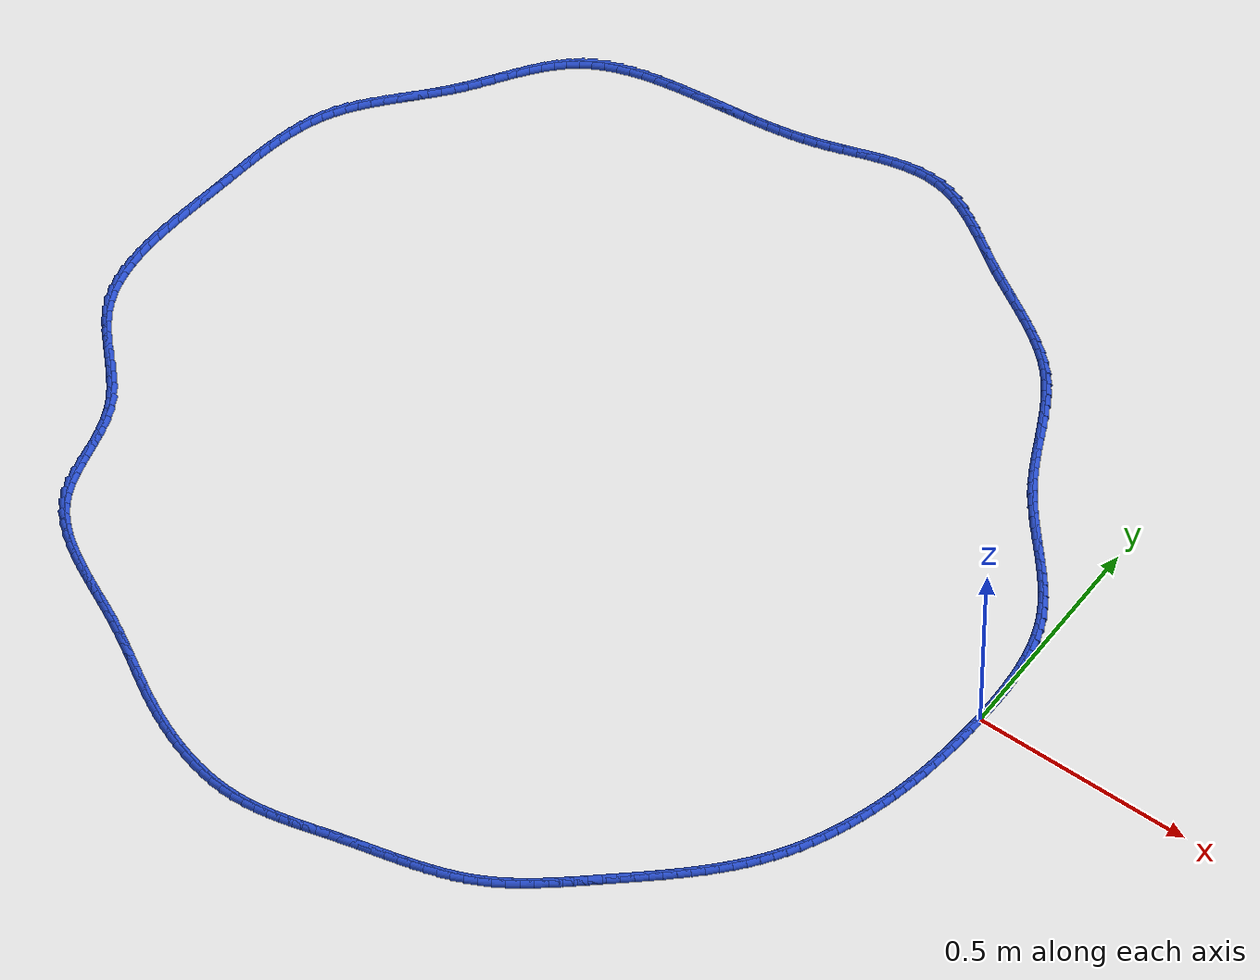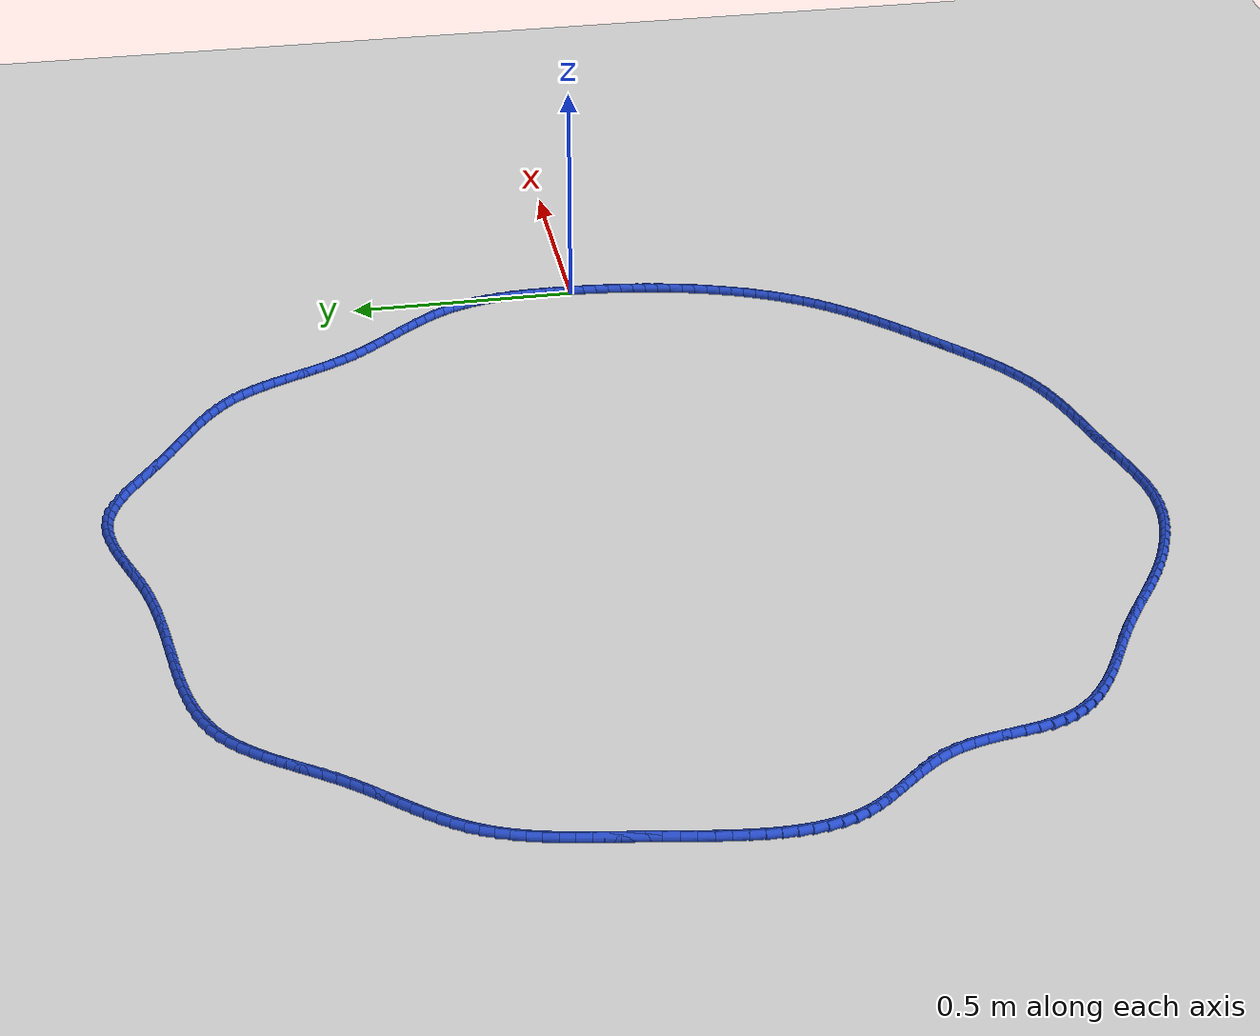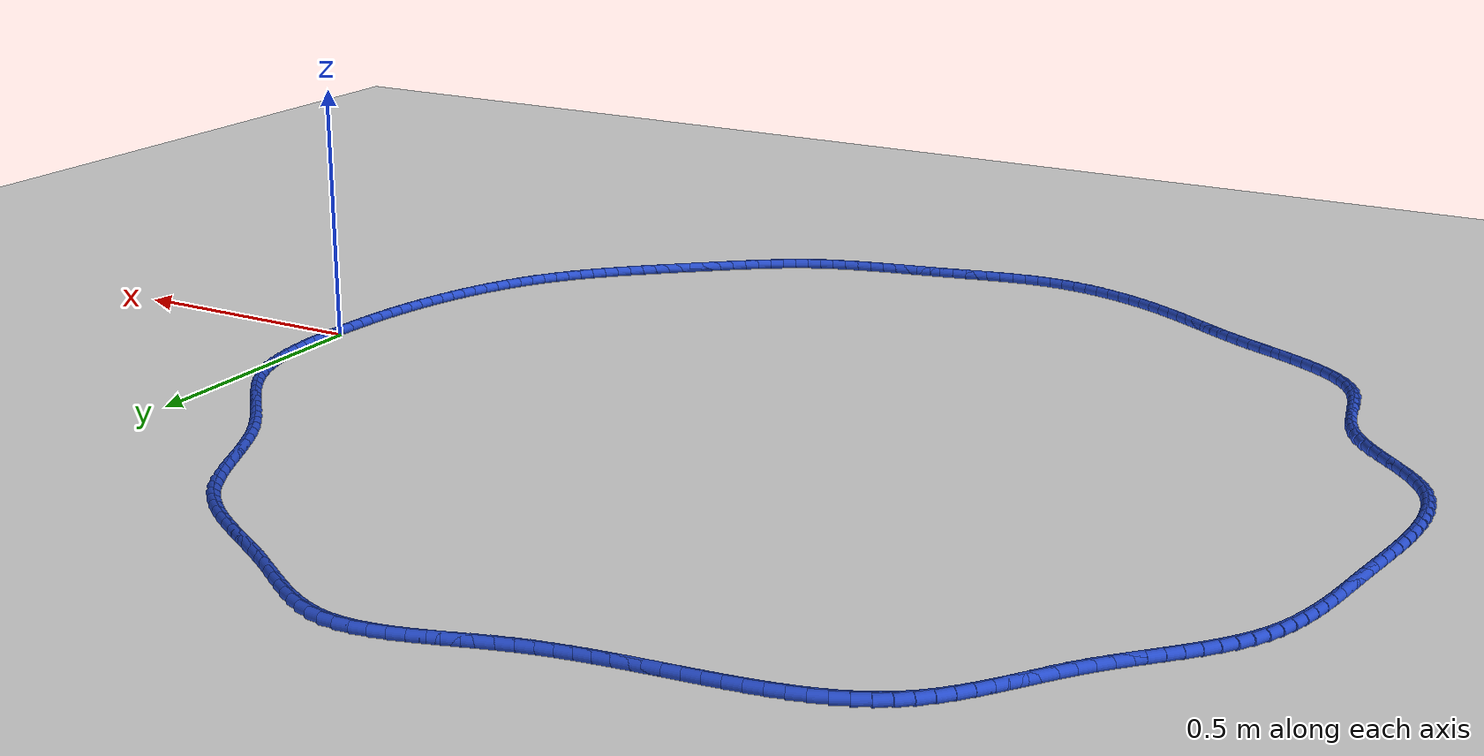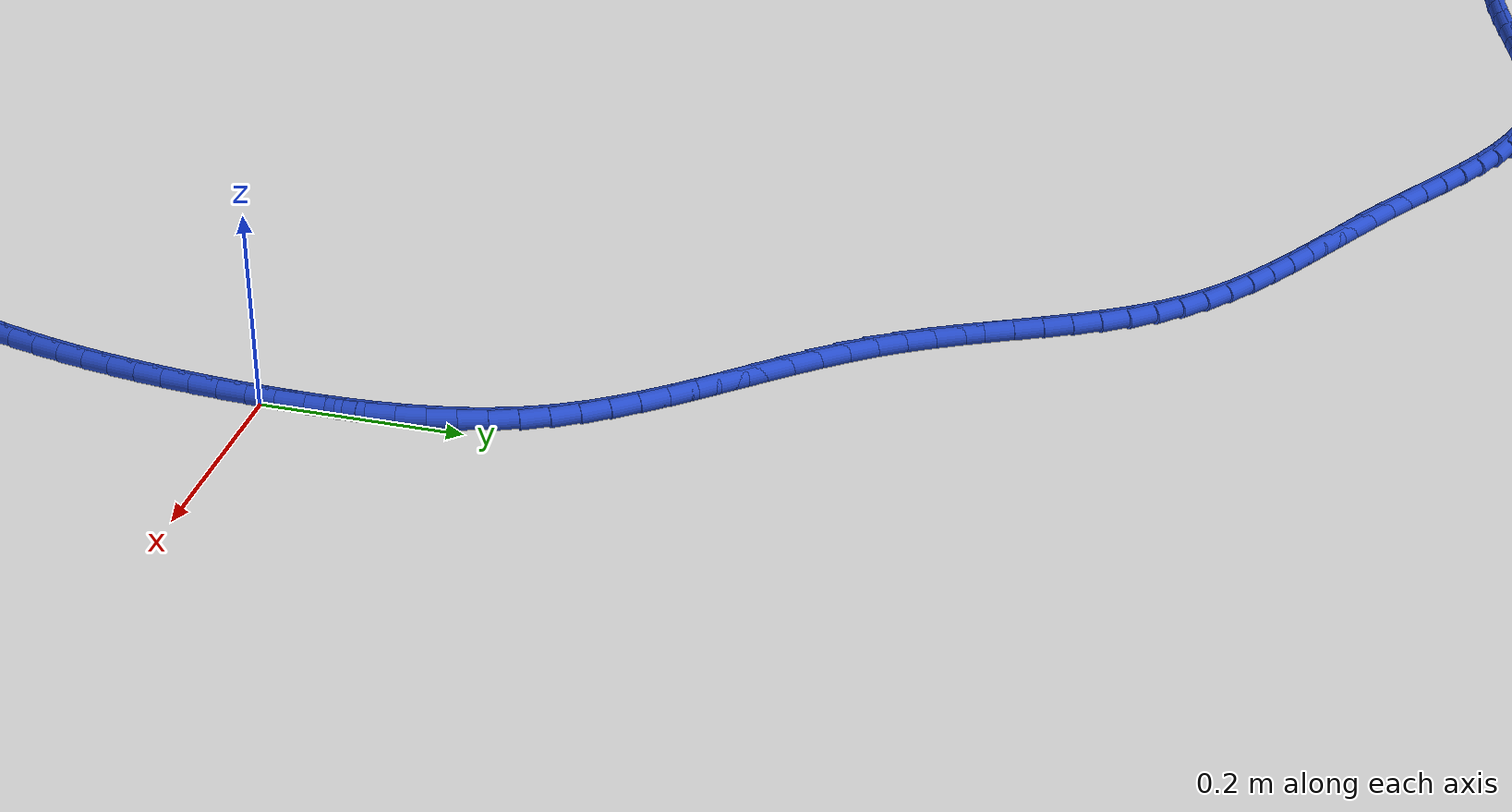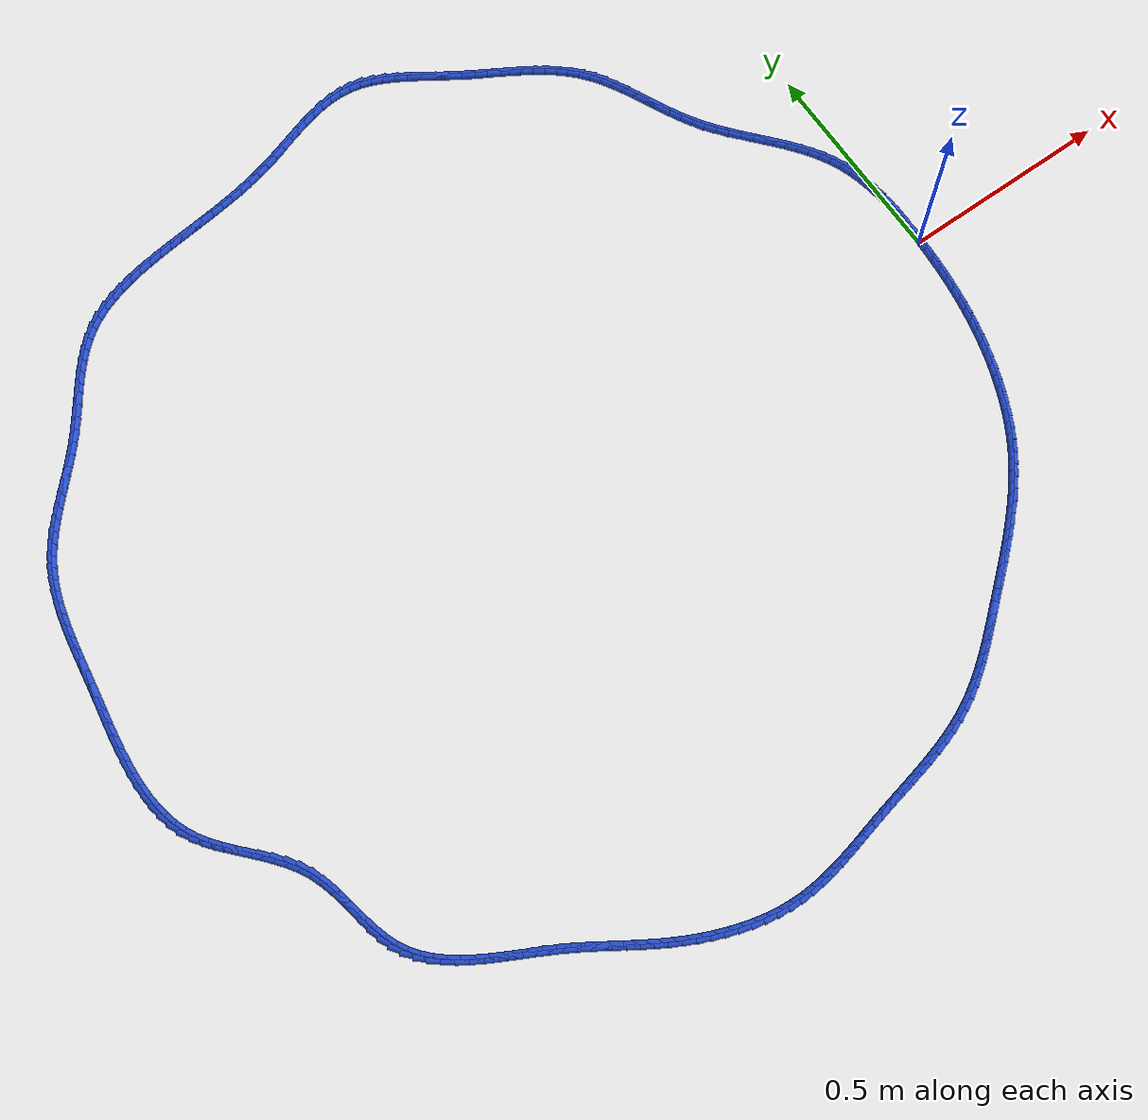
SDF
<sdf version="1.6">
 <world name="default">
  <light name="sun" type="directional">
   <pose>0 0 10 0 -0 0</pose>
   <diffuse>0.8 0.8 0.8 1</diffuse>
   <specular>0.2 0.2 0.2 1</specular>
   <attenuation>
    <range>1000</range>
    <constant>0.9</constant>
    <linear>0.01</linear>
    <quadratic>0.001</quadratic>
   </attenuation>
   <direction>-0.5 0.1 -0.9</direction>
  </light>
  <model name="ground_plane">
   <static>1</static>
   <link name="link">
    <collision name="collision">
     <geometry><plane><normal>0 0 1</normal><size>100 100</size></plane></geometry>
     <surface><friction><ode><mu>100</mu><mu2>50</mu2></ode></friction></surface>
    </collision>
    <visual name="visual">
     <cast_shadows>0</cast_shadows>
     <geometry><plane><normal>0 0 1</normal><size>100 100</size></plane></geometry>
     <material>
      <script><uri>file://media/materials/scripts/gazebo.material</uri><name>Gazebo/WhiteGlow</name></script>
     </material>
    </visual>
   </link>
  </model>
  <gravity>0 0 -9.8</gravity>
  <magnetic_field>6e-06 2.3e-05 -4.2e-05</magnetic_field>
  <atmosphere type="adiabatic"/>
  <physics name="default_physics" default="0" type="ode">
   <max_step_size>0.001</max_step_size>
   <real_time_factor>1</real_time_factor>
   <real_time_update_rate>1000</real_time_update_rate>
  </physics>
  <scene><ambient>0.4 0.4 0.4 1</ambient><background>0.7 0.7 0.7 1</background><shadows>1</shadows></scene>
  <spherical_coordinates>
   <surface_model>EARTH_WGS84</surface_model>
   <latitude_deg>0</latitude_deg>
   <longitude_deg>0</longitude_deg>
   <elevation>0</elevation>
   <heading_deg>0</heading_deg>
  </spherical_coordinates>
  <model name="line">
   <link name="link_0">
    <pose>-6.7220534694101275e-18 4.163336342344337e-17 0.01 0 1.57 1.5436127908950652</pose>
    <collision name="collision">
     <geometry><cylinder><radius>0.01</radius><length>0.08</length></cylinder></geometry>
    </collision>
    <visual name="visual">
     <material>
      <script><name>Gazebo/Blue</name><uri>file://media/materials/scripts/gazebo.material</uri></script>
     </material>
     <geometry><cylinder><radius>0.01</radius><length>0.08</length></cylinder></geometry>
    </visual>
   </link>
   <link name="link_1">
    <pose>0.0007952474365013262 0.029247539705945094 0.01 0 1.57 1.5660994794677434</pose>
    <collision name="collision">
     <geometry><cylinder><radius>0.01</radius><length>0.08</length></cylinder></geometry>
    </collision>
    <visual name="visual">
     <material>
      <script><name>Gazebo/Blue</name><uri>file://media/materials/scripts/gazebo.material</uri></script>
     </material>
     <geometry><cylinder><radius>0.01</radius><length>0.08</length></cylinder></geometry>
    </visual>
   </link>
   <link name="link_2">
    <pose>0.0009331593185395411 0.058609973334598164 0.01 0 1.57 -1.547204821749383</pose>
    <collision name="collision">
     <geometry><cylinder><radius>0.01</radius><length>0.08</length></cylinder></geometry>
    </collision>
    <visual name="visual">
     <material>
      <script><name>Gazebo/Blue</name><uri>file://media/materials/scripts/gazebo.material</uri></script>
     </material>
     <geometry><cylinder><radius>0.01</radius><length>0.08</length></cylinder></geometry>
    </visual>
   </link>
   <link name="link_3">
    <pose>0.00024092148070058725 0.08794720332395434 0.01 0 1.57 -1.5127508872278654</pose>
    <collision name="collision">
     <geometry><cylinder><radius>0.01</radius><length>0.08</length></cylinder></geometry>
    </collision>
    <visual name="visual">
     <material>
      <script><name>Gazebo/Blue</name><uri>file://media/materials/scripts/gazebo.material</uri></script>
     </material>
     <geometry><cylinder><radius>0.01</radius><length>0.08</length></cylinder></geometry>
    </visual>
   </link>
   <link name="link_4">
    <pose>-0.001454280242429589 0.11711913211200858 0.01 0 1.57 -1.4716652824233203</pose>
    <collision name="collision">
     <geometry><cylinder><radius>0.01</radius><length>0.08</length></cylinder></geometry>
    </collision>
    <visual name="visual">
     <material>
      <script><name>Gazebo/Blue</name><uri>file://media/materials/scripts/gazebo.material</uri></script>
     </material>
     <geometry><cylinder><radius>0.01</radius><length>0.08</length></cylinder></geometry>
    </visual>
   </link>
   <link name="link_5">
    <pose>-0.004325260016265041 0.14598566213675607 0.01 0 1.57 -1.423406450708269</pose>
    <collision name="collision">
     <geometry><cylinder><radius>0.01</radius><length>0.08</length></cylinder></geometry>
    </collision>
    <visual name="visual">
     <material>
      <script><name>Gazebo/Blue</name><uri>file://media/materials/scripts/gazebo.material</uri></script>
     </material>
     <geometry><cylinder><radius>0.01</radius><length>0.08</length></cylinder></geometry>
    </visual>
   </link>
   <link name="link_6">
    <pose>-0.008544832006219827 0.1744066958361919 0.01 0 1.57 -1.3674012323876739</pose>
    <collision name="collision">
     <geometry><cylinder><radius>0.01</radius><length>0.08</length></cylinder></geometry>
    </collision>
    <visual name="visual">
     <material>
      <script><name>Gazebo/Blue</name><uri>file://media/materials/scripts/gazebo.material</uri></script>
     </material>
     <geometry><cylinder><radius>0.01</radius><length>0.08</length></cylinder></geometry>
    </visual>
   </link>
   <link name="link_7">
    <pose>-0.014285810377707991 0.20224213564831098 0.01 0 1.57 -1.3031154964479952</pose>
    <collision name="collision">
     <geometry><cylinder><radius>0.01</radius><length>0.08</length></cylinder></geometry>
    </collision>
    <visual name="visual">
     <material>
      <script><name>Gazebo/Blue</name><uri>file://media/materials/scripts/gazebo.material</uri></script>
     </material>
     <geometry><cylinder><radius>0.01</radius><length>0.08</length></cylinder></geometry>
    </visual>
   </link>
   <link name="link_8">
    <pose>-0.02172100929614359 0.22935188401110854 0.01 0 1.57 -1.2301605490318037</pose>
    <collision name="collision">
     <geometry><cylinder><radius>0.01</radius><length>0.08</length></cylinder></geometry>
    </collision>
    <visual name="visual">
     <material>
      <script><name>Gazebo/Blue</name><uri>file://media/materials/scripts/gazebo.material</uri></script>
     </material>
     <geometry><cylinder><radius>0.01</radius><length>0.08</length></cylinder></geometry>
    </visual>
   </link>
   <link name="link_9">
    <pose>-0.031023242926940683 0.25559584336257957 0.01 0 1.57 -1.148730025832334</pose>
    <collision name="collision">
     <geometry><cylinder><radius>0.01</radius><length>0.08</length></cylinder></geometry>
    </collision>
    <visual name="visual">
     <material>
      <script><name>Gazebo/Blue</name><uri>file://media/materials/scripts/gazebo.material</uri></script>
     </material>
     <geometry><cylinder><radius>0.01</radius><length>0.08</length></cylinder></geometry>
    </visual>
   </link>
   <link name="link_10">
    <pose>-0.042358504904863634 0.2808384239106037 0.01 0 1.57 -1.0682264505489718</pose>
    <collision name="collision">
     <geometry><cylinder><radius>0.01</radius><length>0.08</length></cylinder></geometry>
    </collision>
    <visual name="visual">
     <material>
      <script><name>Gazebo/Blue</name><uri>file://media/materials/scripts/gazebo.material</uri></script>
     </material>
     <geometry><cylinder><radius>0.01</radius><length>0.08</length></cylinder></geometry>
    </visual>
   </link>
   <link name="link_11">
    <pose>-0.055683894871363535 0.30508209638950606 0.01 0 1.57 -0.9999975761849269</pose>
    <collision name="collision">
     <geometry><cylinder><radius>0.01</radius><length>0.08</length></cylinder></geometry>
    </collision>
    <visual name="visual">
     <material>
      <script><name>Gazebo/Blue</name><uri>file://media/materials/scripts/gazebo.material</uri></script>
     </material>
     <geometry><cylinder><radius>0.01</radius><length>0.08</length></cylinder></geometry>
    </visual>
   </link>
   <link name="link_12">
    <pose>-0.07071383657959388 0.32848971891652495 0.01 0 1.57 -0.9450374537527997</pose>
    <collision name="collision">
     <geometry><cylinder><radius>0.01</radius><length>0.08</length></cylinder></geometry>
    </collision>
    <visual name="visual">
     <material>
      <script><name>Gazebo/Blue</name><uri>file://media/materials/scripts/gazebo.material</uri></script>
     </material>
     <geometry><cylinder><radius>0.01</radius><length>0.08</length></cylinder></geometry>
    </visual>
   </link>
   <link name="link_13">
    <pose>-0.08714912924655485 0.3512331542270027 0.01 0 1.57 -0.9032056299600782</pose>
    <collision name="collision">
     <geometry><cylinder><radius>0.01</radius><length>0.08</length></cylinder></geometry>
    </collision>
    <visual name="visual">
     <material>
      <script><name>Gazebo/Blue</name><uri>file://media/materials/scripts/gazebo.material</uri></script>
     </material>
     <geometry><cylinder><radius>0.01</radius><length>0.08</length></cylinder></geometry>
    </visual>
   </link>
   <link name="link_14">
    <pose>-0.10469057208924673 0.37348426505628124 0.01 0 1.57 -0.8741007875847613</pose>
    <collision name="collision">
     <geometry><cylinder><radius>0.01</radius><length>0.08</length></cylinder></geometry>
    </collision>
    <visual name="visual">
     <material>
      <script><name>Gazebo/Blue</name><uri>file://media/materials/scripts/gazebo.material</uri></script>
     </material>
     <geometry><cylinder><radius>0.01</radius><length>0.08</length></cylinder></geometry>
    </visual>
   </link>
   <link name="link_15">
    <pose>-0.12303896432466971 0.39541491413970276 0.01 0 1.57 -0.8572731410447892</pose>
    <collision name="collision">
     <geometry><cylinder><radius>0.01</radius><length>0.08</length></cylinder></geometry>
    </collision>
    <visual name="visual">
     <material>
      <script><name>Gazebo/Blue</name><uri>file://media/materials/scripts/gazebo.material</uri></script>
     </material>
     <geometry><cylinder><radius>0.01</radius><length>0.08</length></cylinder></geometry>
    </visual>
   </link>
   <link name="link_16">
    <pose>-0.14189510516982404 0.41719696421260943 0.01 0 1.57 -0.8523550540909516</pose>
    <collision name="collision">
     <geometry><cylinder><radius>0.01</radius><length>0.08</length></cylinder></geometry>
    </collision>
    <visual name="visual">
     <material>
      <script><name>Gazebo/Blue</name><uri>file://media/materials/scripts/gazebo.material</uri></script>
     </material>
     <geometry><cylinder><radius>0.01</radius><length>0.08</length></cylinder></geometry>
    </visual>
   </link>
   <link name="link_17">
    <pose>-0.16095979384170983 0.4390022780103431 0.01 0 1.57 -0.8591250138811715</pose>
    <collision name="collision">
     <geometry><cylinder><radius>0.01</radius><length>0.08</length></cylinder></geometry>
    </collision>
    <visual name="visual">
     <material>
      <script><name>Gazebo/Blue</name><uri>file://media/materials/scripts/gazebo.material</uri></script>
     </material>
     <geometry><cylinder><radius>0.01</radius><length>0.08</length></cylinder></geometry>
    </visual>
   </link>
   <link name="link_18">
    <pose>-0.1799338295573275 0.46100271826824607 0.01 0 1.57 -0.8775200405199837</pose>
    <collision name="collision">
     <geometry><cylinder><radius>0.01</radius><length>0.08</length></cylinder></geometry>
    </collision>
    <visual name="visual">
     <material>
      <script><name>Gazebo/Blue</name><uri>file://media/materials/scripts/gazebo.material</uri></script>
     </material>
     <geometry><cylinder><radius>0.01</radius><length>0.08</length></cylinder></geometry>
    </visual>
   </link>
   <link name="link_19">
    <pose>-0.1985180115336771 0.4833701477216604 0.01 0 1.57 -0.9076043102871109</pose>
    <collision name="collision">
     <geometry><cylinder><radius>0.01</radius><length>0.08</length></cylinder></geometry>
    </collision>
    <visual name="visual">
     <material>
      <script><name>Gazebo/Blue</name><uri>file://media/materials/scripts/gazebo.material</uri></script>
     </material>
     <geometry><cylinder><radius>0.01</radius><length>0.08</length></cylinder></geometry>
    </visual>
   </link>
   <link name="link_20">
    <pose>-0.21641313898775894 0.5062764291059282 0.01 0 1.57 -0.9494937242142367</pose>
    <collision name="collision">
     <geometry><cylinder><radius>0.01</radius><length>0.08</length></cylinder></geometry>
    </collision>
    <visual name="visual">
     <material>
      <script><name>Gazebo/Blue</name><uri>file://media/materials/scripts/gazebo.material</uri></script>
     </material>
     <geometry><cylinder><radius>0.01</radius><length>0.08</length></cylinder></geometry>
    </visual>
   </link>
   <link name="link_21">
    <pose>-0.2333200111365732 0.5298934251563915 0.01 0 1.57 -1.0025591956574016</pose>
    <collision name="collision">
     <geometry><cylinder><radius>0.01</radius><length>0.08</length></cylinder></geometry>
    </collision>
    <visual name="visual">
     <material>
      <script><name>Gazebo/Blue</name><uri>file://media/materials/scripts/gazebo.material</uri></script>
     </material>
     <geometry><cylinder><radius>0.01</radius><length>0.08</length></cylinder></geometry>
    </visual>
   </link>
   <link name="link_22">
    <pose>-0.24895544499840927 0.5543817886077085 0.01 0 1.57 -1.0536971307739194</pose>
    <collision name="collision">
     <geometry><cylinder><radius>0.01</radius><length>0.08</length></cylinder></geometry>
    </collision>
    <visual name="visual">
     <material>
      <script><name>Gazebo/Blue</name><uri>file://media/materials/scripts/gazebo.material</uri></script>
     </material>
     <geometry><cylinder><radius>0.01</radius><length>0.08</length></cylinder></geometry>
    </visual>
   </link>
   <link name="link_23">
    <pose>-0.26334601776941585 0.5796853876469604 0.01 0 1.57 -1.0912162326517247</pose>
    <collision name="collision">
     <geometry><cylinder><radius>0.01</radius><length>0.08</length></cylinder></geometry>
    </collision>
    <visual name="visual">
     <material>
      <script><name>Gazebo/Blue</name><uri>file://media/materials/scripts/gazebo.material</uri></script>
     </material>
     <geometry><cylinder><radius>0.01</radius><length>0.08</length></cylinder></geometry>
    </visual>
   </link>
   <link name="link_24">
    <pose>-0.27679861239916026 0.6055519194867726 0.01 0 1.57 -1.1149260319576053</pose>
    <collision name="collision">
     <geometry><cylinder><radius>0.01</radius><length>0.08</length></cylinder></geometry>
    </collision>
    <visual name="visual">
     <material>
      <script><name>Gazebo/Blue</name><uri>file://media/materials/scripts/gazebo.material</uri></script>
     </material>
     <geometry><cylinder><radius>0.01</radius><length>0.08</length></cylinder></geometry>
    </visual>
   </link>
   <link name="link_25">
    <pose>-0.2896302203112472 0.6317220069605334 0.01 0 1.57 -1.1249902588702205</pose>
    <collision name="collision">
     <geometry><cylinder><radius>0.01</radius><length>0.08</length></cylinder></geometry>
    </collision>
    <visual name="visual">
     <material>
      <script><name>Gazebo/Blue</name><uri>file://media/materials/scripts/gazebo.material</uri></script>
     </material>
     <geometry><cylinder><radius>0.01</radius><length>0.08</length></cylinder></geometry>
    </visual>
   </link>
   <link name="link_26">
    <pose>-0.30215783292928067 0.657936272901631 0.01 0 1.57 -1.1213694451881586</pose>
    <collision name="collision">
     <geometry><cylinder><radius>0.01</radius><length>0.08</length></cylinder></geometry>
    </collision>
    <visual name="visual">
     <material>
      <script><name>Gazebo/Blue</name><uri>file://media/materials/scripts/gazebo.material</uri></script>
     </material>
     <geometry><cylinder><radius>0.01</radius><length>0.08</length></cylinder></geometry>
    </visual>
   </link>
   <link name="link_27">
    <pose>-0.3146984416768654 0.683935340143454 0.01 0 1.57 -1.1037585140640633</pose>
    <collision name="collision">
     <geometry><cylinder><radius>0.01</radius><length>0.08</length></cylinder></geometry>
    </collision>
    <visual name="visual">
     <material>
      <script><name>Gazebo/Blue</name><uri>file://media/materials/scripts/gazebo.material</uri></script>
     </material>
     <geometry><cylinder><radius>0.01</radius><length>0.08</length></cylinder></geometry>
    </visual>
   </link>
   <link name="link_28">
    <pose>-0.3275690379776056 0.7094598315193907 0.01 0 1.57 -1.0715906503778565</pose>
    <collision name="collision">
     <geometry><cylinder><radius>0.01</radius><length>0.08</length></cylinder></geometry>
    </collision>
    <visual name="visual">
     <material>
      <script><name>Gazebo/Blue</name><uri>file://media/materials/scripts/gazebo.material</uri></script>
     </material>
     <geometry><cylinder><radius>0.01</radius><length>0.08</length></cylinder></geometry>
    </visual>
   </link>
   <link name="link_29">
    <pose>-0.3410866132551055 0.7342503698628288 0.01 0 1.57 -1.0241212920625875</pose>
    <collision name="collision">
     <geometry><cylinder><radius>0.01</radius><length>0.08</length></cylinder></geometry>
    </collision>
    <visual name="visual">
     <material>
      <script><name>Gazebo/Blue</name><uri>file://media/materials/scripts/gazebo.material</uri></script>
     </material>
     <geometry><cylinder><radius>0.01</radius><length>0.08</length></cylinder></geometry>
    </visual>
   </link>
   <link name="link_30">
    <pose>-0.3555681589329697 0.7580475780071572 0.01 0 1.57 -0.9606255741254276</pose>
    <collision name="collision">
     <geometry><cylinder><radius>0.01</radius><length>0.08</length></cylinder></geometry>
    </collision>
    <visual name="visual">
     <material>
      <script><name>Gazebo/Blue</name><uri>file://media/materials/scripts/gazebo.material</uri></script>
     </material>
     <geometry><cylinder><radius>0.01</radius><length>0.08</length></cylinder></geometry>
    </visual>
   </link>
   <link name="link_31">
    <pose>-0.3713306664348027 0.7805920787857641 0.01 0 1.57 -0.880944965859874</pose>
    <collision name="collision">
     <geometry><cylinder><radius>0.01</radius><length>0.08</length></cylinder></geometry>
    </collision>
    <visual name="visual">
     <material>
      <script><name>Gazebo/Blue</name><uri>file://media/materials/scripts/gazebo.material</uri></script>
     </material>
     <geometry><cylinder><radius>0.01</radius><length>0.08</length></cylinder></geometry>
    </visual>
   </link>
   <link name="link_32">
    <pose>-0.3886872609580348 0.8016281760271757 0.01 0 1.57 -0.7956933365458116</pose>
    <collision name="collision">
     <geometry><cylinder><radius>0.01</radius><length>0.08</length></cylinder></geometry>
    </collision>
    <visual name="visual">
     <material>
      <script><name>Gazebo/Blue</name><uri>file://media/materials/scripts/gazebo.material</uri></script>
     </material>
     <geometry><cylinder><radius>0.01</radius><length>0.08</length></cylinder></geometry>
    </visual>
   </link>
   <link name="link_33">
    <pose>-0.40775207182667306 0.821089635533862 0.01 0 1.57 -0.7209084457540363</pose>
    <collision name="collision">
     <geometry><cylinder><radius>0.01</radius><length>0.08</length></cylinder></geometry>
    </collision>
    <visual name="visual">
     <material>
      <script><name>Gazebo/Blue</name><uri>file://media/materials/scripts/gazebo.material</uri></script>
     </material>
     <geometry><cylinder><radius>0.01</radius><length>0.08</length></cylinder></geometry>
    </visual>
   </link>
   <link name="link_34">
    <pose>-0.4283483857234254 0.8391871314681452 0.01 0 1.57 -0.6585102063815033</pose>
    <collision name="collision">
     <geometry><cylinder><radius>0.01</radius><length>0.08</length></cylinder></geometry>
    </collision>
    <visual name="visual">
     <material>
      <script><name>Gazebo/Blue</name><uri>file://media/materials/scripts/gazebo.material</uri></script>
     </material>
     <geometry><cylinder><radius>0.01</radius><length>0.08</length></cylinder></geometry>
    </visual>
   </link>
   <link name="link_35">
    <pose>-0.45027642037944005 0.8561533017096057 0.01 0 1.57 -0.6085544483917543</pose>
    <collision name="collision">
     <geometry><cylinder><radius>0.01</radius><length>0.08</length></cylinder></geometry>
    </collision>
    <visual name="visual">
     <material>
      <script><name>Gazebo/Blue</name><uri>file://media/materials/scripts/gazebo.material</uri></script>
     </material>
     <geometry><cylinder><radius>0.01</radius><length>0.08</length></cylinder></geometry>
    </visual>
   </link>
   <link name="link_36">
    <pose>-0.47333639352586554 0.8722207841378238 0.01 0 1.57 -0.5706860413022776</pose>
    <collision name="collision">
     <geometry><cylinder><radius>0.01</radius><length>0.08</length></cylinder></geometry>
    </collision>
    <visual name="visual">
     <material>
      <script><name>Gazebo/Blue</name><uri>file://media/materials/scripts/gazebo.material</uri></script>
     </material>
     <geometry><cylinder><radius>0.01</radius><length>0.08</length></cylinder></geometry>
    </visual>
   </link>
   <link name="link_37">
    <pose>-0.49732852289385004 0.8876222166323794 0.01 0 1.57 -0.5443748927801129</pose>
    <collision name="collision">
     <geometry><cylinder><radius>0.01</radius><length>0.08</length></cylinder></geometry>
    </collision>
    <visual name="visual">
     <material>
      <script><name>Gazebo/Blue</name><uri>file://media/materials/scripts/gazebo.material</uri></script>
     </material>
     <geometry><cylinder><radius>0.01</radius><length>0.08</length></cylinder></geometry>
    </visual>
   </link>
   <link name="link_38">
    <pose>-0.5220530262145419 0.9025902370728528 0.01 0 1.57 -0.5290765007022975</pose>
    <collision name="collision">
     <geometry><cylinder><radius>0.01</radius><length>0.08</length></cylinder></geometry>
    </collision>
    <visual name="visual">
     <material>
      <script><name>Gazebo/Blue</name><uri>file://media/materials/scripts/gazebo.material</uri></script>
     </material>
     <geometry><cylinder><radius>0.01</radius><length>0.08</length></cylinder></geometry>
    </visual>
   </link>
   <link name="link_39">
    <pose>-0.5473101212190895 0.9173574833388245 0.01 0 1.57 -0.5243244929143375</pose>
    <collision name="collision">
     <geometry><cylinder><radius>0.01</radius><length>0.08</length></cylinder></geometry>
    </collision>
    <visual name="visual">
     <material>
      <script><name>Gazebo/Blue</name><uri>file://media/materials/scripts/gazebo.material</uri></script>
     </material>
     <geometry><cylinder><radius>0.01</radius><length>0.08</length></cylinder></geometry>
    </visual>
   </link>
   <link name="link_40">
    <pose>-0.5729000256386412 0.9321565933098743 0.01 0 1.57 -0.529771580305207</pose>
    <collision name="collision">
     <geometry><cylinder><radius>0.01</radius><length>0.08</length></cylinder></geometry>
    </collision>
    <visual name="visual">
     <material>
      <script><name>Gazebo/Blue</name><uri>file://media/materials/scripts/gazebo.material</uri></script>
     </material>
     <geometry><cylinder><radius>0.01</radius><length>0.08</length></cylinder></geometry>
    </visual>
   </link>
   <link name="link_41">
    <pose>-0.5986229572043453 0.9472202048655824 0.01 0 1.57 -0.5451931883106077</pose>
    <collision name="collision">
     <geometry><cylinder><radius>0.01</radius><length>0.08</length></cylinder></geometry>
    </collision>
    <visual name="visual">
     <material>
      <script><name>Gazebo/Blue</name><uri>file://media/materials/scripts/gazebo.material</uri></script>
     </material>
     <geometry><cylinder><radius>0.01</radius><length>0.08</length></cylinder></geometry>
    </visual>
   </link>
   <link name="link_42">
    <pose>-0.62427913364735 0.9627809558855289 0.01 0 1.57 -0.5679532677448654</pose>
    <collision name="collision">
     <geometry><cylinder><radius>0.01</radius><length>0.08</length></cylinder></geometry>
    </collision>
    <visual name="visual">
     <material>
      <script><name>Gazebo/Blue</name><uri>file://media/materials/scripts/gazebo.material</uri></script>
     </material>
     <geometry><cylinder><radius>0.01</radius><length>0.08</length></cylinder></geometry>
    </visual>
   </link>
   <link name="link_43">
    <pose>-0.6496974149469981 0.9789999727362018 0.01 0 1.57 -0.5817536383395939</pose>
    <collision name="collision">
     <geometry><cylinder><radius>0.01</radius><length>0.08</length></cylinder></geometry>
    </collision>
    <visual name="visual">
     <material>
      <script><name>Gazebo/Blue</name><uri>file://media/materials/scripts/gazebo.material</uri></script>
     </material>
     <geometry><cylinder><radius>0.01</radius><length>0.08</length></cylinder></geometry>
    </visual>
   </link>
   <link name="link_44">
    <pose>-0.6748938239948943 0.9955710894486532 0.01 0 1.57 -0.580198200061795</pose>
    <collision name="collision">
     <geometry><cylinder><radius>0.01</radius><length>0.08</length></cylinder></geometry>
    </collision>
    <visual name="visual">
     <material>
      <script><name>Gazebo/Blue</name><uri>file://media/materials/scripts/gazebo.material</uri></script>
     </material>
     <geometry><cylinder><radius>0.01</radius><length>0.08</length></cylinder></geometry>
    </visual>
   </link>
   <link name="link_45">
    <pose>-0.6999595523793434 1.0120004652875638 0.01 0 1.57 -0.5629480627219295</pose>
    <collision name="collision">
     <geometry><cylinder><radius>0.01</radius><length>0.08</length></cylinder></geometry>
    </collision>
    <visual name="visual">
     <material>
      <script><name>Gazebo/Blue</name><uri>file://media/materials/scripts/gazebo.material</uri></script>
     </material>
     <geometry><cylinder><radius>0.01</radius><length>0.08</length></cylinder></geometry>
    </visual>
   </link>
   <link name="link_46">
    <pose>-0.7249859949085495 1.0277937521355693 0.01 0 1.57 -0.5290763161988603</pose>
    <collision name="collision">
     <geometry><cylinder><radius>0.01</radius><length>0.08</length></cylinder></geometry>
    </collision>
    <visual name="visual">
     <material>
      <script><name>Gazebo/Blue</name><uri>file://media/materials/scripts/gazebo.material</uri></script>
     </material>
     <geometry><cylinder><radius>0.01</radius><length>0.08</length></cylinder></geometry>
    </visual>
   </link>
   <link name="link_47">
    <pose>-0.750064546390716 1.0424566018753052 0.01 0 1.57 -0.47710055481302543</pose>
    <collision name="collision">
     <geometry><cylinder><radius>0.01</radius><length>0.08</length></cylinder></geometry>
    </collision>
    <visual name="visual">
     <material>
      <script><name>Gazebo/Blue</name><uri>file://media/materials/scripts/gazebo.material</uri></script>
     </material>
     <geometry><cylinder><radius>0.01</radius><length>0.08</length></cylinder></geometry>
    </visual>
   </link>
   <link name="link_48">
    <pose>-0.7752866016340467 1.0554946663894065 0.01 0 1.57 -0.40518406008961466</pose>
    <collision name="collision">
     <geometry><cylinder><radius>0.01</radius><length>0.08</length></cylinder></geometry>
    </collision>
    <visual name="visual">
     <material>
      <script><name>Gazebo/Blue</name><uri>file://media/materials/scripts/gazebo.material</uri></script>
     </material>
     <geometry><cylinder><radius>0.01</radius><length>0.08</length></cylinder></geometry>
    </visual>
   </link>
   <link name="link_49">
    <pose>-0.8007435554467452 1.0664135975605085 0.01 0 1.57 -0.3116301116305825</pose>
    <collision name="collision">
     <geometry><cylinder><radius>0.01</radius><length>0.08</length></cylinder></geometry>
    </collision>
    <visual name="visual">
     <material>
      <script><name>Gazebo/Blue</name><uri>file://media/materials/scripts/gazebo.material</uri></script>
     </material>
     <geometry><cylinder><radius>0.01</radius><length>0.08</length></cylinder></geometry>
    </visual>
   </link>
   <link name="link_50">
    <pose>-0.826526802637016 1.0747190472712473 0.01 0 1.57 -0.19583292439934197</pose>
    <collision name="collision">
     <geometry><cylinder><radius>0.01</radius><length>0.08</length></cylinder></geometry>
    </collision>
    <visual name="visual">
     <material>
      <script><name>Gazebo/Blue</name><uri>file://media/materials/scripts/gazebo.material</uri></script>
     </material>
     <geometry><cylinder><radius>0.01</radius><length>0.08</length></cylinder></geometry>
    </visual>
   </link>
   <link name="link_51">
    <pose>-0.8527277380130621 1.079916667404258 0.01 0 1.57 -0.06571365874950474</pose>
    <collision name="collision">
     <geometry><cylinder><radius>0.01</radius><length>0.08</length></cylinder></geometry>
    </collision>
    <visual name="visual">
     <material>
      <script><name>Gazebo/Blue</name><uri>file://media/materials/scripts/gazebo.material</uri></script>
     </material>
     <geometry><cylinder><radius>0.01</radius><length>0.08</length></cylinder></geometry>
    </visual>
   </link>
   <link name="link_52">
    <pose>-0.8794116943631914 1.0816726962115064 0.01 0 1.57 0.04994334118425181</pose>
    <collision name="collision">
     <geometry><cylinder><radius>0.01</radius><length>0.08</length></cylinder></geometry>
    </collision>
    <visual name="visual">
     <material>
      <script><name>Gazebo/Blue</name><uri>file://media/materials/scripts/gazebo.material</uri></script>
     </material>
     <geometry><cylinder><radius>0.01</radius><length>0.08</length></cylinder></geometry>
    </visual>
   </link>
   <link name="link_53">
    <pose>-0.9065363228090589 1.080316874158518 0.01 0 1.57 0.14327675265308007</pose>
    <collision name="collision">
     <geometry><cylinder><radius>0.01</radius><length>0.08</length></cylinder></geometry>
    </collision>
    <visual name="visual">
     <material>
      <script><name>Gazebo/Blue</name><uri>file://media/materials/scripts/gazebo.material</uri></script>
     </material>
     <geometry><cylinder><radius>0.01</radius><length>0.08</length></cylinder></geometry>
    </visual>
   </link>
   <link name="link_54">
    <pose>-0.9340314675741436 1.0763502794980788 0.01 0 1.57 0.2152211155103689</pose>
    <collision name="collision">
     <geometry><cylinder><radius>0.01</radius><length>0.08</length></cylinder></geometry>
    </collision>
    <visual name="visual">
     <material>
      <script><name>Gazebo/Blue</name><uri>file://media/materials/scripts/gazebo.material</uri></script>
     </material>
     <geometry><cylinder><radius>0.01</radius><length>0.08</length></cylinder></geometry>
    </visual>
   </link>
   <link name="link_55">
    <pose>-0.9618269728479942 1.070273990692036 0.01 0 1.57 0.26763076164166005</pose>
    <collision name="collision">
     <geometry><cylinder><radius>0.01</radius><length>0.08</length></cylinder></geometry>
    </collision>
    <visual name="visual">
     <material>
      <script><name>Gazebo/Blue</name><uri>file://media/materials/scripts/gazebo.material</uri></script>
     </material>
     <geometry><cylinder><radius>0.01</radius><length>0.08</length></cylinder></geometry>
    </visual>
   </link>
   <link name="link_56">
    <pose>-0.9898526828201601 1.0625890862022378 0.01 0 1.57 0.3023803026855797</pose>
    <collision name="collision">
     <geometry><cylinder><radius>0.01</radius><length>0.08</length></cylinder></geometry>
    </collision>
    <visual name="visual">
     <material>
      <script><name>Gazebo/Blue</name><uri>file://media/materials/scripts/gazebo.material</uri></script>
     </material>
     <geometry><cylinder><radius>0.01</radius><length>0.08</length></cylinder></geometry>
    </visual>
   </link>
   <link name="link_57">
    <pose>-1.0180384416801902 1.0537966444905325 0.01 0 1.57 0.3209126686316605</pose>
    <collision name="collision">
     <geometry><cylinder><radius>0.01</radius><length>0.08</length></cylinder></geometry>
    </collision>
    <visual name="visual">
     <material>
      <script><name>Gazebo/Blue</name><uri>file://media/materials/scripts/gazebo.material</uri></script>
     </material>
     <geometry><cylinder><radius>0.01</radius><length>0.08</length></cylinder></geometry>
    </visual>
   </link>
   <link name="link_58">
    <pose>-1.0463140936176338 1.0443977440187677 0.01 0 1.57 0.3240543120813352</pose>
    <collision name="collision">
     <geometry><cylinder><radius>0.01</radius><length>0.08</length></cylinder></geometry>
    </collision>
    <visual name="visual">
     <material>
      <script><name>Gazebo/Blue</name><uri>file://media/materials/scripts/gazebo.material</uri></script>
     </material>
     <geometry><cylinder><radius>0.01</radius><length>0.08</length></cylinder></geometry>
    </visual>
   </link>
   <link name="link_59">
    <pose>-1.0746094828220407 1.0348934632487918 0.01 0 1.57 0.31195559259773376</pose>
    <collision name="collision">
     <geometry><cylinder><radius>0.01</radius><length>0.08</length></cylinder></geometry>
    </collision>
    <visual name="visual">
     <material>
      <script><name>Gazebo/Blue</name><uri>file://media/materials/scripts/gazebo.material</uri></script>
     </material>
     <geometry><cylinder><radius>0.01</radius><length>0.08</length></cylinder></geometry>
    </visual>
   </link>
   <link name="link_60">
    <pose>-1.1028544534829592 1.025784880642453 0.01 0 1.57 0.2842858949782381</pose>
    <collision name="collision">
     <geometry><cylinder><radius>0.01</radius><length>0.08</length></cylinder></geometry>
    </collision>
    <visual name="visual">
     <material>
      <script><name>Gazebo/Blue</name><uri>file://media/materials/scripts/gazebo.material</uri></script>
     </material>
     <geometry><cylinder><radius>0.01</radius><length>0.08</length></cylinder></geometry>
    </visual>
   </link>
   <link name="link_61">
    <pose>-1.1309800457159738 1.0175665723268508 0.01 0 1.57 0.24844615764061057</pose>
    <collision name="collision">
     <geometry><cylinder><radius>0.01</radius><length>0.08</length></cylinder></geometry>
    </collision>
    <visual name="visual">
     <material>
      <script><name>Gazebo/Blue</name><uri>file://media/materials/scripts/gazebo.material</uri></script>
     </material>
     <geometry><cylinder><radius>0.01</radius><length>0.08</length></cylinder></geometry>
    </visual>
   </link>
   <link name="link_62">
    <pose>-1.1589662777002083 1.0104668172208588 0.01 0 1.57 0.2155462210586795</pose>
    <collision name="collision">
     <geometry><cylinder><radius>0.01</radius><length>0.08</length></cylinder></geometry>
    </collision>
    <visual name="visual">
     <material>
      <script><name>Gazebo/Blue</name><uri>file://media/materials/scripts/gazebo.material</uri></script>
     </material>
     <geometry><cylinder><radius>0.01</radius><length>0.08</length></cylinder></geometry>
    </visual>
   </link>
   <link name="link_63">
    <pose>-1.1868582688744531 1.0043599340732465 0.01 0 1.57 0.1868319856758696</pose>
    <collision name="collision">
     <geometry><cylinder><radius>0.01</radius><length>0.08</length></cylinder></geometry>
    </collision>
    <visual name="visual">
     <material>
      <script><name>Gazebo/Blue</name><uri>file://media/materials/scripts/gazebo.material</uri></script>
     </material>
     <geometry><cylinder><radius>0.01</radius><length>0.08</length></cylinder></geometry>
    </visual>
   </link>
   <link name="link_64">
    <pose>-1.214705641324465 0.9990957604216043 0.01 0 1.57 0.1626871165350177</pose>
    <collision name="collision">
     <geometry><cylinder><radius>0.01</radius><length>0.08</length></cylinder></geometry>
    </collision>
    <visual name="visual">
     <material>
      <script><name>Gazebo/Blue</name><uri>file://media/materials/scripts/gazebo.material</uri></script>
     </material>
     <geometry><cylinder><radius>0.01</radius><length>0.08</length></cylinder></geometry>
    </visual>
   </link>
   <link name="link_65">
    <pose>-1.242558017136001 0.9945241338035207 0.01 0 1.57 0.14339016053336223</pose>
    <collision name="collision">
     <geometry><cylinder><radius>0.01</radius><length>0.08</length></cylinder></geometry>
    </collision>
    <visual name="visual">
     <material>
      <script><name>Gazebo/Blue</name><uri>file://media/materials/scripts/gazebo.material</uri></script>
     </material>
     <geometry><cylinder><radius>0.01</radius><length>0.08</length></cylinder></geometry>
    </visual>
   </link>
   <link name="link_66">
    <pose>-1.270465018394818 0.990494891756585 0.01 0 1.57 0.1291190429775601</pose>
    <collision name="collision">
     <geometry><cylinder><radius>0.01</radius><length>0.08</length></cylinder></geometry>
    </collision>
    <visual name="visual">
     <material>
      <script><name>Gazebo/Blue</name><uri>file://media/materials/scripts/gazebo.material</uri></script>
     </material>
     <geometry><cylinder><radius>0.01</radius><length>0.08</length></cylinder></geometry>
    </visual>
   </link>
   <link name="link_67">
    <pose>-1.2984762671866734 0.9868578718183878 0.01 0 1.57 0.1199590187277706</pose>
    <collision name="collision">
     <geometry><cylinder><radius>0.01</radius><length>0.08</length></cylinder></geometry>
    </collision>
    <visual name="visual">
     <material>
      <script><name>Gazebo/Blue</name><uri>file://media/materials/scripts/gazebo.material</uri></script>
     </material>
     <geometry><cylinder><radius>0.01</radius><length>0.08</length></cylinder></geometry>
    </visual>
   </link>
   <link name="link_68">
    <pose>-1.3266413855973231 0.9834629115265174 0.01 0 1.57 0.11591181261026348</pose>
    <collision name="collision">
     <geometry><cylinder><radius>0.01</radius><length>0.08</length></cylinder></geometry>
    </collision>
    <visual name="visual">
     <material>
      <script><name>Gazebo/Blue</name><uri>file://media/materials/scripts/gazebo.material</uri></script>
     </material>
     <geometry><cylinder><radius>0.01</radius><length>0.08</length></cylinder></geometry>
    </visual>
   </link>
   <link name="link_69">
    <pose>-1.3550099957125252 0.9801598484185645 0.01 0 1.57 0.11690427085240773</pose>
    <collision name="collision">
     <geometry><cylinder><radius>0.01</radius><length>0.08</length></cylinder></geometry>
    </collision>
    <visual name="visual">
     <material>
      <script><name>Gazebo/Blue</name><uri>file://media/materials/scripts/gazebo.material</uri></script>
     </material>
     <geometry><cylinder><radius>0.01</radius><length>0.08</length></cylinder></geometry>
    </visual>
   </link>
   <link name="link_70">
    <pose>-1.3836317196180357 0.9767985200321178 0.01 0 1.57 0.1228278778570988</pose>
    <collision name="collision">
     <geometry><cylinder><radius>0.01</radius><length>0.08</length></cylinder></geometry>
    </collision>
    <visual name="visual">
     <material>
      <script><name>Gazebo/Blue</name><uri>file://media/materials/scripts/gazebo.material</uri></script>
     </material>
     <geometry><cylinder><radius>0.01</radius><length>0.08</length></cylinder></geometry>
    </visual>
   </link>
   <link name="link_71">
    <pose>-1.4125535657635688 0.9732281378815058 0.01 0 1.57 0.13486666835451985</pose>
    <collision name="collision">
     <geometry><cylinder><radius>0.01</radius><length>0.08</length></cylinder></geometry>
    </collision>
    <visual name="visual">
     <material>
      <script><name>Gazebo/Blue</name><uri>file://media/materials/scripts/gazebo.material</uri></script>
     </material>
     <geometry><cylinder><radius>0.01</radius><length>0.08</length></cylinder></geometry>
    </visual>
   </link>
   <link name="link_72">
    <pose>-1.441712488704288 0.969271553155115 0.01 0 1.57 0.15483810672446255</pose>
    <collision name="collision">
     <geometry><cylinder><radius>0.01</radius><length>0.08</length></cylinder></geometry>
    </collision>
    <visual name="visual">
     <material>
      <script><name>Gazebo/Blue</name><uri>file://media/materials/scripts/gazebo.material</uri></script>
     </material>
     <geometry><cylinder><radius>0.01</radius><length>0.08</length></cylinder></geometry>
    </visual>
   </link>
   <link name="link_73">
    <pose>-1.4708973897423008 0.9647161550340773 0.01 0 1.57 0.18314148890919707</pose>
    <collision name="collision">
     <geometry><cylinder><radius>0.01</radius><length>0.08</length></cylinder></geometry>
    </collision>
    <visual name="visual">
     <material>
      <script><name>Gazebo/Blue</name><uri>file://media/materials/scripts/gazebo.material</uri></script>
     </material>
     <geometry><cylinder><radius>0.01</radius><length>0.08</length></cylinder></geometry>
    </visual>
   </link>
   <link name="link_74">
    <pose>-1.4998867464685015 0.9593468359916473 0.01 0 1.57 0.22030091998594417</pose>
    <collision name="collision">
     <geometry><cylinder><radius>0.01</radius><length>0.08</length></cylinder></geometry>
    </collision>
    <visual name="visual">
     <material>
      <script><name>Gazebo/Blue</name><uri>file://media/materials/scripts/gazebo.material</uri></script>
     </material>
     <geometry><cylinder><radius>0.01</radius><length>0.08</length></cylinder></geometry>
    </visual>
   </link>
   <link name="link_75">
    <pose>-1.5284590364737827 0.9529484885010825 0.01 0 1.57 0.2670582784661351</pose>
    <collision name="collision">
     <geometry><cylinder><radius>0.01</radius><length>0.08</length></cylinder></geometry>
    </collision>
    <visual name="visual">
     <material>
      <script><name>Gazebo/Blue</name><uri>file://media/materials/scripts/gazebo.material</uri></script>
     </material>
     <geometry><cylinder><radius>0.01</radius><length>0.08</length></cylinder></geometry>
    </visual>
   </link>
   <link name="link_76">
    <pose>-1.5563927373490378 0.9453060050356383 0.01 0 1.57 0.3243146006801603</pose>
    <collision name="collision">
     <geometry><cylinder><radius>0.01</radius><length>0.08</length></cylinder></geometry>
    </collision>
    <visual name="visual">
     <material>
      <script><name>Gazebo/Blue</name><uri>file://media/materials/scripts/gazebo.material</uri></script>
     </material>
     <geometry><cylinder><radius>0.01</radius><length>0.08</length></cylinder></geometry>
    </visual>
   </link>
   <link name="link_77">
    <pose>-1.5834663266851607 0.9362042780685707 0.01 0 1.57 0.39302275209202026</pose>
    <collision name="collision">
     <geometry><cylinder><radius>0.01</radius><length>0.08</length></cylinder></geometry>
    </collision>
    <visual name="visual">
     <material>
      <script><name>Gazebo/Blue</name><uri>file://media/materials/scripts/gazebo.material</uri></script>
     </material>
     <geometry><cylinder><radius>0.01</radius><length>0.08</length></cylinder></geometry>
    </visual>
   </link>
   <link name="link_78">
    <pose>-1.6094582820730456 0.9254282000731366 0.01 0 1.57 0.4739992963055898</pose>
    <collision name="collision">
     <geometry><cylinder><radius>0.01</radius><length>0.08</length></cylinder></geometry>
    </collision>
    <visual name="visual">
     <material>
      <script><name>Gazebo/Blue</name><uri>file://media/materials/scripts/gazebo.material</uri></script>
     </material>
     <geometry><cylinder><radius>0.01</radius><length>0.08</length></cylinder></geometry>
    </visual>
   </link>
   <link name="link_79">
    <pose>-1.6341470811035848 0.9127626635225913 0.01 0 1.57 0.5676241114362008</pose>
    <collision name="collision">
     <geometry><cylinder><radius>0.01</radius><length>0.08</length></cylinder></geometry>
    </collision>
    <visual name="visual">
     <material>
      <script><name>Gazebo/Blue</name><uri>file://media/materials/scripts/gazebo.material</uri></script>
     </material>
     <geometry><cylinder><radius>0.01</radius><length>0.08</length></cylinder></geometry>
    </visual>
   </link>
   <link name="link_80">
    <pose>-1.6573112931341238 0.8979926606103238 0.01 0 1.57 0.6675223752436715</pose>
    <collision name="collision">
     <geometry><cylinder><radius>0.01</radius><length>0.08</length></cylinder></geometry>
    </collision>
    <visual name="visual">
     <material>
      <script><name>Gazebo/Blue</name><uri>file://media/materials/scripts/gazebo.material</uri></script>
     </material>
     <geometry><cylinder><radius>0.01</radius><length>0.08</length></cylinder></geometry>
    </visual>
   </link>
   <link name="link_81">
    <pose>-1.6788399083577752 0.881023174879361 0.01 0 1.57 0.7547705717098283</pose>
    <collision name="collision">
     <geometry><cylinder><radius>0.01</radius><length>0.08</length></cylinder></geometry>
    </collision>
    <visual name="visual">
     <material>
      <script><name>Gazebo/Blue</name><uri>file://media/materials/scripts/gazebo.material</uri></script>
     </material>
     <geometry><cylinder><radius>0.01</radius><length>0.08</length></cylinder></geometry>
    </visual>
   </link>
   <link name="link_82">
    <pose>-1.698946535724557 0.8621119443369386 0.01 0 1.57 0.8252152059311931</pose>
    <collision name="collision">
     <geometry><cylinder><radius>0.01</radius><length>0.08</length></cylinder></geometry>
    </collision>
    <visual name="visual">
     <material>
      <script><name>Gazebo/Blue</name><uri>file://media/materials/scripts/gazebo.material</uri></script>
     </material>
     <geometry><cylinder><radius>0.01</radius><length>0.08</length></cylinder></geometry>
    </visual>
   </link>
   <link name="link_83">
    <pose>-1.717904136305009 0.8415812033418729 0.01 0 1.57 0.8789981842940865</pose>
    <collision name="collision">
     <geometry><cylinder><radius>0.01</radius><length>0.08</length></cylinder></geometry>
    </collision>
    <visual name="visual">
     <material>
      <script><name>Gazebo/Blue</name><uri>file://media/materials/scripts/gazebo.material</uri></script>
     </material>
     <geometry><cylinder><radius>0.01</radius><length>0.08</length></cylinder></geometry>
    </visual>
   </link>
   <link name="link_84">
    <pose>-1.735985671169673 0.8197531862529825 0.01 0 1.57 0.91682173868104</pose>
    <collision name="collision">
     <geometry><cylinder><radius>0.01</radius><length>0.08</length></cylinder></geometry>
    </collision>
    <visual name="visual">
     <material>
      <script><name>Gazebo/Blue</name><uri>file://media/materials/scripts/gazebo.material</uri></script>
     </material>
     <geometry><cylinder><radius>0.01</radius><length>0.08</length></cylinder></geometry>
    </visual>
   </link>
   <link name="link_85">
    <pose>-1.7534641013890924 0.7969501274290836 0.01 0 1.57 0.9395096066476771</pose>
    <collision name="collision">
     <geometry><cylinder><radius>0.01</radius><length>0.08</length></cylinder></geometry>
    </collision>
    <visual name="visual">
     <material>
      <script><name>Gazebo/Blue</name><uri>file://media/materials/scripts/gazebo.material</uri></script>
     </material>
     <geometry><cylinder><radius>0.01</radius><length>0.08</length></cylinder></geometry>
    </visual>
   </link>
   <link name="link_86">
    <pose>-1.770612388033807 0.7734942612289942 0.01 0 1.57 0.9477466765565931</pose>
    <collision name="collision">
     <geometry><cylinder><radius>0.01</radius><length>0.08</length></cylinder></geometry>
    </collision>
    <visual name="visual">
     <material>
      <script><name>Gazebo/Blue</name><uri>file://media/materials/scripts/gazebo.material</uri></script>
     </material>
     <geometry><cylinder><radius>0.01</radius><length>0.08</length></cylinder></geometry>
    </visual>
   </link>
   <link name="link_87">
    <pose>-1.7877034921743586 0.7497078220115316 0.01 0 1.57 0.9419563450467623</pose>
    <collision name="collision">
     <geometry><cylinder><radius>0.01</radius><length>0.08</length></cylinder></geometry>
    </collision>
    <visual name="visual">
     <material>
      <script><name>Gazebo/Blue</name><uri>file://media/materials/scripts/gazebo.material</uri></script>
     </material>
     <geometry><cylinder><radius>0.01</radius><length>0.08</length></cylinder></geometry>
    </visual>
   </link>
   <link name="link_88">
    <pose>-1.8050103748812898 0.7259130441355124 0.01 0 1.57 0.9222729205326368</pose>
    <collision name="collision">
     <geometry><cylinder><radius>0.01</radius><length>0.08</length></cylinder></geometry>
    </collision>
    <visual name="visual">
     <material>
      <script><name>Gazebo/Blue</name><uri>file://media/materials/scripts/gazebo.material</uri></script>
     </material>
     <geometry><cylinder><radius>0.01</radius><length>0.08</length></cylinder></geometry>
    </visual>
   </link>
   <link name="link_89">
    <pose>-1.8228059972251407 0.7024321619597547 0.01 0 1.57 0.8891310103549633</pose>
    <collision name="collision">
     <geometry><cylinder><radius>0.01</radius><length>0.08</length></cylinder></geometry>
    </collision>
    <visual name="visual">
     <material>
      <script><name>Gazebo/Blue</name><uri>file://media/materials/scripts/gazebo.material</uri></script>
     </material>
     <geometry><cylinder><radius>0.01</radius><length>0.08</length></cylinder></geometry>
    </visual>
   </link>
   <link name="link_90">
    <pose>-1.8413513482412776 0.67957671791348 0.01 0 1.57 0.8546655504393275</pose>
    <collision name="collision">
     <geometry><cylinder><radius>0.01</radius><length>0.08</length></cylinder></geometry>
    </collision>
    <visual name="visual">
     <material>
      <script><name>Gazebo/Blue</name><uri>file://media/materials/scripts/gazebo.material</uri></script>
     </material>
     <geometry><cylinder><radius>0.01</radius><length>0.08</length></cylinder></geometry>
    </visual>
   </link>
   <link name="link_91">
    <pose>-1.8606364130896305 0.6574162275429698 0.01 0 1.57 0.8310324120451116</pose>
    <collision name="collision">
     <geometry><cylinder><radius>0.01</radius><length>0.08</length></cylinder></geometry>
    </collision>
    <visual name="visual">
     <material>
      <script><name>Gazebo/Blue</name><uri>file://media/materials/scripts/gazebo.material</uri></script>
     </material>
     <geometry><cylinder><radius>0.01</radius><length>0.08</length></cylinder></geometry>
    </visual>
   </link>
   <link name="link_92">
    <pose>-1.8803825695163372 0.6357803197324008 0.01 0 1.57 0.8187480232031066</pose>
    <collision name="collision">
     <geometry><cylinder><radius>0.01</radius><length>0.08</length></cylinder></geometry>
    </collision>
    <visual name="visual">
     <material>
      <script><name>Gazebo/Blue</name><uri>file://media/materials/scripts/gazebo.material</uri></script>
     </material>
     <geometry><cylinder><radius>0.01</radius><length>0.08</length></cylinder></geometry>
    </visual>
   </link>
   <link name="link_93">
    <pose>-1.9002997025365393 0.6144883594911081 0.01 0 1.57 0.817899839012565</pose>
    <collision name="collision">
     <geometry><cylinder><radius>0.01</radius><length>0.08</length></cylinder></geometry>
    </collision>
    <visual name="visual">
     <material>
      <script><name>Gazebo/Blue</name><uri>file://media/materials/scripts/gazebo.material</uri></script>
     </material>
     <geometry><cylinder><radius>0.01</radius><length>0.08</length></cylinder></geometry>
    </visual>
   </link>
   <link name="link_94">
    <pose>-1.9200976971653796 0.5933597118284263 0.01 0 1.57 0.8287222479016721</pose>
    <collision name="collision">
     <geometry><cylinder><radius>0.01</radius><length>0.08</length></cylinder></geometry>
    </collision>
    <visual name="visual">
     <material>
      <script><name>Gazebo/Blue</name><uri>file://media/materials/scripts/gazebo.material</uri></script>
     </material>
     <geometry><cylinder><radius>0.01</radius><length>0.08</length></cylinder></geometry>
    </visual>
   </link>
   <link name="link_95">
    <pose>-1.939486438418 0.5722137417536911 0.01 0 1.57 0.8516098982184807</pose>
    <collision name="collision">
     <geometry><cylinder><radius>0.01</radius><length>0.08</length></cylinder></geometry>
    </collision>
    <visual name="visual">
     <material>
      <script><name>Gazebo/Blue</name><uri>file://media/materials/scripts/gazebo.material</uri></script>
     </material>
     <geometry><cylinder><radius>0.01</radius><length>0.08</length></cylinder></geometry>
    </visual>
   </link>
   <link name="link_96">
    <pose>-1.9581758113095433 0.5508698142762366 0.01 0 1.57 0.8870853955643602</pose>
    <collision name="collision">
     <geometry><cylinder><radius>0.01</radius><length>0.08</length></cylinder></geometry>
    </collision>
    <visual name="visual">
     <material>
      <script><name>Gazebo/Blue</name><uri>file://media/materials/scripts/gazebo.material</uri></script>
     </material>
     <geometry><cylinder><radius>0.01</radius><length>0.08</length></cylinder></geometry>
    </visual>
   </link>
   <link name="link_97">
    <pose>-1.9758757008551513 0.5291472944053985 0.01 0 1.57 0.9357067175996127</pose>
    <collision name="collision">
     <geometry><cylinder><radius>0.01</radius><length>0.08</length></cylinder></geometry>
    </collision>
    <visual name="visual">
     <material>
      <script><name>Gazebo/Blue</name><uri>file://media/materials/scripts/gazebo.material</uri></script>
     </material>
     <geometry><cylinder><radius>0.01</radius><length>0.08</length></cylinder></geometry>
    </visual>
   </link>
   <link name="link_98">
    <pose>-1.9922959920699665 0.5068655471505116 0.01 0 1.57 0.9978937823005347</pose>
    <collision name="collision">
     <geometry><cylinder><radius>0.01</radius><length>0.08</length></cylinder></geometry>
    </collision>
    <visual name="visual">
     <material>
      <script><name>Gazebo/Blue</name><uri>file://media/materials/scripts/gazebo.material</uri></script>
     </material>
     <geometry><cylinder><radius>0.01</radius><length>0.08</length></cylinder></geometry>
    </visual>
   </link>
   <link name="link_99">
    <pose>-2.0071465699691315 0.48384393752091015 0.01 0 1.57 1.0725974394548579</pose>
    <collision name="collision">
     <geometry><cylinder><radius>0.01</radius><length>0.08</length></cylinder></geometry>
    </collision>
    <visual name="visual">
     <material>
      <script><name>Gazebo/Blue</name><uri>file://media/materials/scripts/gazebo.material</uri></script>
     </material>
     <geometry><cylinder><radius>0.01</radius><length>0.08</length></cylinder></geometry>
    </visual>
   </link>
   <link name="link_100">
    <pose>-2.0201632019851767 0.45991481563457653 0.01 0 1.57 1.1471839814776899</pose>
    <collision name="collision">
     <geometry><cylinder><radius>0.01</radius><length>0.08</length></cylinder></geometry>
    </collision>
    <visual name="visual">
     <material>
      <script><name>Gazebo/Blue</name><uri>file://media/materials/scripts/gazebo.material</uri></script>
     </material>
     <geometry><cylinder><radius>0.01</radius><length>0.08</length></cylinder></geometry>
    </visual>
   </link>
   <link name="link_101">
    <pose>-2.031372211600938 0.4350563024555601 0.01 0 1.57 1.213182689610502</pose>
    <collision name="collision">
     <geometry><cylinder><radius>0.01</radius><length>0.08</length></cylinder></geometry>
    </collision>
    <visual name="visual">
     <material>
      <script><name>Gazebo/Blue</name><uri>file://media/materials/scripts/gazebo.material</uri></script>
     </material>
     <geometry><cylinder><radius>0.01</radius><length>0.08</length></cylinder></geometry>
    </visual>
   </link>
   <link name="link_102">
    <pose>-2.0409825878626315 0.40933816155419867 0.01 0 1.57 1.269965993674583</pose>
    <collision name="collision">
     <geometry><cylinder><radius>0.01</radius><length>0.08</length></cylinder></geometry>
    </collision>
    <visual name="visual">
     <material>
      <script><name>Gazebo/Blue</name><uri>file://media/materials/scripts/gazebo.material</uri></script>
     </material>
     <geometry><cylinder><radius>0.01</radius><length>0.08</length></cylinder></geometry>
    </visual>
   </link>
   <link name="link_103">
    <pose>-2.0492061560994013 0.3828315794529955 0.01 0 1.57 1.3174473876385244</pose>
    <collision name="collision">
     <geometry><cylinder><radius>0.01</radius><length>0.08</length></cylinder></geometry>
    </collision>
    <visual name="visual">
     <material>
      <script><name>Gazebo/Blue</name><uri>file://media/materials/scripts/gazebo.material</uri></script>
     </material>
     <geometry><cylinder><radius>0.01</radius><length>0.08</length></cylinder></geometry>
    </visual>
   </link>
   <link name="link_104">
    <pose>-2.0562547416403874 0.35560774267445505 0.01 0 1.57 1.3558192131780582</pose>
    <collision name="collision">
     <geometry><cylinder><radius>0.01</radius><length>0.08</length></cylinder></geometry>
    </collision>
    <visual name="visual">
     <material>
      <script><name>Gazebo/Blue</name><uri>file://media/materials/scripts/gazebo.material</uri></script>
     </material>
     <geometry><cylinder><radius>0.01</radius><length>0.08</length></cylinder></geometry>
    </visual>
   </link>
   <link name="link_105">
    <pose>-2.0623401698147323 0.32773783774108034 0.01 0 1.57 1.38542464925822</pose>
    <collision name="collision">
     <geometry><cylinder><radius>0.01</radius><length>0.08</length></cylinder></geometry>
    </collision>
    <visual name="visual">
     <material>
      <script><name>Gazebo/Blue</name><uri>file://media/materials/scripts/gazebo.material</uri></script>
     </material>
     <geometry><cylinder><radius>0.01</radius><length>0.08</length></cylinder></geometry>
    </visual>
   </link>
   <link name="link_106">
    <pose>-2.0676742659515757 0.29929305117537575 0.01 0 1.57 1.4066614295665194</pose>
    <collision name="collision">
     <geometry><cylinder><radius>0.01</radius><length>0.08</length></cylinder></geometry>
    </collision>
    <visual name="visual">
     <material>
      <script><name>Gazebo/Blue</name><uri>file://media/materials/scripts/gazebo.material</uri></script>
     </material>
     <geometry><cylinder><radius>0.01</radius><length>0.08</length></cylinder></geometry>
    </visual>
   </link>
   <link name="link_107">
    <pose>-2.0724688553800608 0.2703445694998446 0.01 0 1.57 1.419917780522216</pose>
    <collision name="collision">
     <geometry><cylinder><radius>0.01</radius><length>0.08</length></cylinder></geometry>
    </collision>
    <visual name="visual">
     <material>
      <script><name>Gazebo/Blue</name><uri>file://media/materials/scripts/gazebo.material</uri></script>
     </material>
     <geometry><cylinder><radius>0.01</radius><length>0.08</length></cylinder></geometry>
    </visual>
   </link>
   <link name="link_108">
    <pose>-2.0769357634293284 0.24096357923699047 0.01 0 1.57 1.4255350837176197</pose>
    <collision name="collision">
     <geometry><cylinder><radius>0.01</radius><length>0.08</length></cylinder></geometry>
    </collision>
    <visual name="visual">
     <material>
      <script><name>Gazebo/Blue</name><uri>file://media/materials/scripts/gazebo.material</uri></script>
     </material>
     <geometry><cylinder><radius>0.01</radius><length>0.08</length></cylinder></geometry>
    </visual>
   </link>
   <link name="link_109">
    <pose>-2.081286815428518 0.21122126690931753 0.01 0 1.57 1.4237906389219697</pose>
    <collision name="collision">
     <geometry><cylinder><radius>0.01</radius><length>0.08</length></cylinder></geometry>
    </collision>
    <visual name="visual">
     <material>
      <script><name>Gazebo/Blue</name><uri>file://media/materials/scripts/gazebo.material</uri></script>
     </material>
     <geometry><cylinder><radius>0.01</radius><length>0.08</length></cylinder></geometry>
    </visual>
   </link>
   <link name="link_110">
    <pose>-2.0857338367067735 0.1811888190393291 0.01 0 1.57 1.417181414850975</pose>
    <collision name="collision">
     <geometry><cylinder><radius>0.01</radius><length>0.08</length></cylinder></geometry>
    </collision>
    <visual name="visual">
     <material>
      <script><name>Gazebo/Blue</name><uri>file://media/materials/scripts/gazebo.material</uri></script>
     </material>
     <geometry><cylinder><radius>0.01</radius><length>0.08</length></cylinder></geometry>
    </visual>
   </link>
   <link name="link_111">
    <pose>-2.09041708596897 0.15094205849736314 0.01 0 1.57 1.4152018193870985</pose>
    <collision name="collision">
     <geometry><cylinder><radius>0.01</radius><length>0.08</length></cylinder></geometry>
    </collision>
    <visual name="visual">
     <material>
      <script><name>Gazebo/Blue</name><uri>file://media/materials/scripts/gazebo.material</uri></script>
     </material>
     <geometry><cylinder><radius>0.01</radius><length>0.08</length></cylinder></geometry>
    </visual>
   </link>
   <link name="link_112">
    <pose>-2.095180377261493 0.12057601292363712 0.01 0 1.57 1.4202137347952972</pose>
    <collision name="collision">
     <geometry><cylinder><radius>0.01</radius><length>0.08</length></cylinder></geometry>
    </collision>
    <visual name="visual">
     <material>
      <script><name>Gazebo/Blue</name><uri>file://media/materials/scripts/gazebo.material</uri></script>
     </material>
     <geometry><cylinder><radius>0.01</radius><length>0.08</length></cylinder></geometry>
    </visual>
   </link>
   <link name="link_113">
    <pose>-2.099790779103971 0.0901906818144603 0.01 0 1.57 1.4322851072332323</pose>
    <collision name="collision">
     <geometry><cylinder><radius>0.01</radius><length>0.08</length></cylinder></geometry>
    </collision>
    <visual name="visual">
     <material>
      <script><name>Gazebo/Blue</name><uri>file://media/materials/scripts/gazebo.material</uri></script>
     </material>
     <geometry><cylinder><radius>0.01</radius><length>0.08</length></cylinder></geometry>
    </visual>
   </link>
   <link name="link_114">
    <pose>-2.1040153598989844 0.05988606467372346 0.01 0 1.57 1.451663254664725</pose>
    <collision name="collision">
     <geometry><cylinder><radius>0.01</radius><length>0.08</length></cylinder></geometry>
    </collision>
    <visual name="visual">
     <material>
      <script><name>Gazebo/Blue</name><uri>file://media/materials/scripts/gazebo.material</uri></script>
     </material>
     <geometry><cylinder><radius>0.01</radius><length>0.08</length></cylinder></geometry>
    </visual>
   </link>
   <link name="link_115">
    <pose>-2.1076211880491087 0.029762161005318845 0.01 0 1.57 1.4787698170864698</pose>
    <collision name="collision">
     <geometry><cylinder><radius>0.01</radius><length>0.08</length></cylinder></geometry>
    </collision>
    <visual name="visual">
     <material>
      <script><name>Gazebo/Blue</name><uri>file://media/materials/scripts/gazebo.material</uri></script>
     </material>
     <geometry><cylinder><radius>0.01</radius><length>0.08</length></cylinder></geometry>
    </visual>
   </link>
   <link name="link_116">
    <pose>-2.1103753319569254 -8.102968686240185e-05 0.01 0 1.57 1.5141906161627725</pose>
    <collision name="collision">
     <geometry><cylinder><radius>0.01</radius><length>0.08</length></cylinder></geometry>
    </collision>
    <visual name="visual">
     <material>
      <script><name>Gazebo/Blue</name><uri>file://media/materials/scripts/gazebo.material</uri></script>
     </material>
     <geometry><cylinder><radius>0.01</radius><length>0.08</length></cylinder></geometry>
    </visual>
   </link>
   <link name="link_117">
    <pose>-2.1120448600250117 -0.02954350789892954 0.01 0 1.57 1.5586520246102968</pose>
    <collision name="collision">
     <geometry><cylinder><radius>0.01</radius><length>0.08</length></cylinder></geometry>
    </collision>
    <visual name="visual">
     <material>
      <script><name>Gazebo/Blue</name><uri>file://media/materials/scripts/gazebo.material</uri></script>
     </material>
     <geometry><cylinder><radius>0.01</radius><length>0.08</length></cylinder></geometry>
    </visual>
   </link>
   <link name="link_118">
    <pose>-2.112396840655945 -0.058525274126989525 0.01 0 1.57 -1.528622268116091</pose>
    <collision name="collision">
     <geometry><cylinder><radius>0.01</radius><length>0.08</length></cylinder></geometry>
    </collision>
    <visual name="visual">
     <material>
      <script><name>Gazebo/Blue</name><uri>file://media/materials/scripts/gazebo.material</uri></script>
     </material>
     <geometry><cylinder><radius>0.01</radius><length>0.08</length></cylinder></geometry>
    </visual>
   </link>
   <link name="link_119">
    <pose>-2.1111983422523037 -0.08692632886715163 0.01 0 1.57 -1.4636372491875962</pose>
    <collision name="collision">
     <geometry><cylinder><radius>0.01</radius><length>0.08</length></cylinder></geometry>
    </collision>
    <visual name="visual">
     <material>
      <script><name>Gazebo/Blue</name><uri>file://media/materials/scripts/gazebo.material</uri></script>
     </material>
     <geometry><cylinder><radius>0.01</radius><length>0.08</length></cylinder></geometry>
    </visual>
   </link>
   <link name="link_120">
    <pose>-2.108216433216669 -0.11464667261552436 0.01 0 1.57 -1.387347084543055</pose>
    <collision name="collision">
     <geometry><cylinder><radius>0.01</radius><length>0.08</length></cylinder></geometry>
    </collision>
    <visual name="visual">
     <material>
      <script><name>Gazebo/Blue</name><uri>file://media/materials/scripts/gazebo.material</uri></script>
     </material>
     <geometry><cylinder><radius>0.01</radius><length>0.08</length></cylinder></geometry>
    </visual>
   </link>
   <link name="link_121">
    <pose>-2.103218181951615 -0.1415863058682162 0.01 0 1.57 -1.2995311785305668</pose>
    <collision name="collision">
     <geometry><cylinder><radius>0.01</radius><length>0.08</length></cylinder></geometry>
    </collision>
    <visual name="visual">
     <material>
      <script><name>Gazebo/Blue</name><uri>file://media/materials/scripts/gazebo.material</uri></script>
     </material>
     <geometry><cylinder><radius>0.01</radius><length>0.08</length></cylinder></geometry>
    </visual>
   </link>
   <link name="link_122">
    <pose>-2.0959706568597225 -0.1676452291213362 0.01 0 1.57 -1.2006987515562726</pose>
    <collision name="collision">
     <geometry><cylinder><radius>0.01</radius><length>0.08</length></cylinder></geometry>
    </collision>
    <visual name="visual">
     <material>
      <script><name>Gazebo/Blue</name><uri>file://media/materials/scripts/gazebo.material</uri></script>
     </material>
     <geometry><cylinder><radius>0.01</radius><length>0.08</length></cylinder></geometry>
    </visual>
   </link>
   <link name="link_123">
    <pose>-2.0862409263435704 -0.1927234428709917 0.01 0 1.57 -1.092426177666422</pose>
    <collision name="collision">
     <geometry><cylinder><radius>0.01</radius><length>0.08</length></cylinder></geometry>
    </collision>
    <visual name="visual">
     <material>
      <script><name>Gazebo/Blue</name><uri>file://media/materials/scripts/gazebo.material</uri></script>
     </material>
     <geometry><cylinder><radius>0.01</radius><length>0.08</length></cylinder></geometry>
    </visual>
   </link>
   <link name="link_124">
    <pose>-2.0737970120260285 -0.21672137999701563 0.01 0 1.57 -0.9871279708148253</pose>
    <collision name="collision">
     <geometry><cylinder><radius>0.01</radius><length>0.08</length></cylinder></geometry>
    </collision>
    <visual name="visual">
     <material>
      <script><name>Gazebo/Blue</name><uri>file://media/materials/scripts/gazebo.material</uri></script>
     </material>
     <geometry><cylinder><radius>0.01</radius><length>0.08</length></cylinder></geometry>
    </visual>
   </link>
   <link name="link_125">
    <pose>-2.058653523191849 -0.23965132631854175 0.01 0 1.57 -0.9086593959951932</pose>
    <collision name="collision">
     <geometry><cylinder><radius>0.01</radius><length>0.08</length></cylinder></geometry>
    </collision>
    <visual name="visual">
     <material>
      <script><name>Gazebo/Blue</name><uri>file://media/materials/scripts/gazebo.material</uri></script>
     </material>
     <geometry><cylinder><radius>0.01</radius><length>0.08</length></cylinder></geometry>
    </visual>
   </link>
   <link name="link_126">
    <pose>-2.041398890343728 -0.26178585476465327 0.01 0 1.57 -0.858455662096106</pose>
    <collision name="collision">
     <geometry><cylinder><radius>0.01</radius><length>0.08</length></cylinder></geometry>
    </collision>
    <visual name="visual">
     <material>
      <script><name>Gazebo/Blue</name><uri>file://media/materials/scripts/gazebo.material</uri></script>
     </material>
     <geometry><cylinder><radius>0.01</radius><length>0.08</length></cylinder></geometry>
    </visual>
   </link>
   <link name="link_127">
    <pose>-2.022702988753618 -0.2834344818680272 0.01 0 1.57 -0.8343324402039474</pose>
    <collision name="collision">
     <geometry><cylinder><radius>0.01</radius><length>0.08</length></cylinder></geometry>
    </collision>
    <visual name="visual">
     <material>
      <script><name>Gazebo/Blue</name><uri>file://media/materials/scripts/gazebo.material</uri></script>
     </material>
     <geometry><cylinder><radius>0.01</radius><length>0.08</length></cylinder></geometry>
    </visual>
   </link>
   <link name="link_128">
    <pose>-2.0032356936934694 -0.3049067241613425 0.01 0 1.57 -0.8348199616858903</pose>
    <collision name="collision">
     <geometry><cylinder><radius>0.01</radius><length>0.08</length></cylinder></geometry>
    </collision>
    <visual name="visual">
     <material>
      <script><name>Gazebo/Blue</name><uri>file://media/materials/scripts/gazebo.material</uri></script>
     </material>
     <geometry><cylinder><radius>0.01</radius><length>0.08</length></cylinder></geometry>
    </visual>
   </link>
   <link name="link_129">
    <pose>-1.9836668804352358 -0.3265120981772772 0.01 0 1.57 -0.8595052975661128</pose>
    <collision name="collision">
     <geometry><cylinder><radius>0.01</radius><length>0.08</length></cylinder></geometry>
    </collision>
    <visual name="visual">
     <material>
      <script><name>Gazebo/Blue</name><uri>file://media/materials/scripts/gazebo.material</uri></script>
     </material>
     <geometry><cylinder><radius>0.01</radius><length>0.08</length></cylinder></geometry>
    </visual>
   </link>
   <link name="link_130">
    <pose>-1.9646664242508693 -0.3485601204485097 0.01 0 1.57 -0.9089681022972401</pose>
    <collision name="collision">
     <geometry><cylinder><radius>0.01</radius><length>0.08</length></cylinder></geometry>
    </collision>
    <visual name="visual">
     <material>
      <script><name>Gazebo/Blue</name><uri>file://media/materials/scripts/gazebo.material</uri></script>
     </material>
     <geometry><cylinder><radius>0.01</radius><length>0.08</length></cylinder></geometry>
    </visual>
   </link>
   <link name="link_131">
    <pose>-1.9469042004123218 -0.3713603075077189 0.01 0 1.57 -0.9843561394557979</pose>
    <collision name="collision">
     <geometry><cylinder><radius>0.01</radius><length>0.08</length></cylinder></geometry>
    </collision>
    <visual name="visual">
     <material>
      <script><name>Gazebo/Blue</name><uri>file://media/materials/scripts/gazebo.material</uri></script>
     </material>
     <geometry><cylinder><radius>0.01</radius><length>0.08</length></cylinder></geometry>
    </visual>
   </link>
   <link name="link_132">
    <pose>-1.9310500841915452 -0.39522217588758163 0.01 0 1.57 -1.0863880887117086</pose>
    <collision name="collision">
     <geometry><cylinder><radius>0.01</radius><length>0.08</length></cylinder></geometry>
    </collision>
    <visual name="visual">
     <material>
      <script><name>Gazebo/Blue</name><uri>file://media/materials/scripts/gazebo.material</uri></script>
     </material>
     <geometry><cylinder><radius>0.01</radius><length>0.08</length></cylinder></geometry>
    </visual>
   </link>
   <link name="link_133">
    <pose>-1.9177722435402444 -0.42045433953218814 0.01 0 1.57 -1.1985998933821502</pose>
    <collision name="collision">
     <geometry><cylinder><radius>0.01</radius><length>0.08</length></cylinder></geometry>
    </collision>
    <visual name="visual">
     <material>
      <script><name>Gazebo/Blue</name><uri>file://media/materials/scripts/gazebo.material</uri></script>
     </material>
     <geometry><cylinder><radius>0.01</radius><length>0.08</length></cylinder></geometry>
    </visual>
   </link>
   <link name="link_134">
    <pose>-1.907347200558816 -0.4471583656545684 0.01 0 1.57 -1.2845496479250111</pose>
    <collision name="collision">
     <geometry><cylinder><radius>0.01</radius><length>0.08</length></cylinder></geometry>
    </collision>
    <visual name="visual">
     <material>
      <script><name>Gazebo/Blue</name><uri>file://media/materials/scripts/gazebo.material</uri></script>
     </material>
     <geometry><cylinder><radius>0.01</radius><length>0.08</length></cylinder></geometry>
    </visual>
   </link>
   <link name="link_135">
    <pose>-1.8991626105600103 -0.4749659148873171 0.01 0 1.57 -1.340423242050216</pose>
    <collision name="collision">
     <geometry><cylinder><radius>0.01</radius><length>0.08</length></cylinder></geometry>
    </collision>
    <visual name="visual">
     <material>
      <script><name>Gazebo/Blue</name><uri>file://media/materials/scripts/gazebo.material</uri></script>
     </material>
     <geometry><cylinder><radius>0.01</radius><length>0.08</length></cylinder></geometry>
    </visual>
   </link>
   <link name="link_136">
    <pose>-1.8924834912622064 -0.5034438145118381 0.01 0 1.57 -1.3678612541677018</pose>
    <collision name="collision">
     <geometry><cylinder><radius>0.01</radius><length>0.08</length></cylinder></geometry>
    </collision>
    <visual name="visual">
     <material>
      <script><name>Gazebo/Blue</name><uri>file://media/materials/scripts/gazebo.material</uri></script>
     </material>
     <geometry><cylinder><radius>0.01</radius><length>0.08</length></cylinder></geometry>
    </visual>
   </link>
   <link name="link_137">
    <pose>-1.8865748603837853 -0.5321588918095376 0.01 0 1.57 -1.3676990048068947</pose>
    <collision name="collision">
     <geometry><cylinder><radius>0.01</radius><length>0.08</length></cylinder></geometry>
    </collision>
    <visual name="visual">
     <material>
      <script><name>Gazebo/Blue</name><uri>file://media/materials/scripts/gazebo.material</uri></script>
     </material>
     <geometry><cylinder><radius>0.01</radius><length>0.08</length></cylinder></geometry>
    </visual>
   </link>
   <link name="link_138">
    <pose>-1.8807017356431261 -0.5606779740618212 0.01 0 1.57 -1.3393568377235328</pose>
    <collision name="collision">
     <geometry><cylinder><radius>0.01</radius><length>0.08</length></cylinder></geometry>
    </collision>
    <visual name="visual">
     <material>
      <script><name>Gazebo/Blue</name><uri>file://media/materials/scripts/gazebo.material</uri></script>
     </material>
     <geometry><cylinder><radius>0.01</radius><length>0.08</length></cylinder></geometry>
    </visual>
   </link>
   <link name="link_139">
    <pose>-1.87412913475861 -0.5885678885500945 0.01 0 1.57 -1.2807494980696872</pose>
    <collision name="collision">
     <geometry><cylinder><radius>0.01</radius><length>0.08</length></cylinder></geometry>
    </collision>
    <visual name="visual">
     <material>
      <script><name>Gazebo/Blue</name><uri>file://media/materials/scripts/gazebo.material</uri></script>
     </material>
     <geometry><cylinder><radius>0.01</radius><length>0.08</length></cylinder></geometry>
    </visual>
   </link>
   <link name="link_140">
    <pose>-1.8661220754486165 -0.6153954625557637 0.01 0 1.57 -1.1888045173449513</pose>
    <collision name="collision">
     <geometry><cylinder><radius>0.01</radius><length>0.08</length></cylinder></geometry>
    </collision>
    <visual name="visual">
     <material>
      <script><name>Gazebo/Blue</name><uri>file://media/materials/scripts/gazebo.material</uri></script>
     </material>
     <geometry><cylinder><radius>0.01</radius><length>0.08</length></cylinder></geometry>
    </visual>
   </link>
   <link name="link_141">
    <pose>-1.8559455754315253 -0.6407275233602328 0.01 0 1.57 -1.063014744393864</pose>
    <collision name="collision">
     <geometry><cylinder><radius>0.01</radius><length>0.08</length></cylinder></geometry>
    </collision>
    <visual name="visual">
     <material>
      <script><name>Gazebo/Blue</name><uri>file://media/materials/scripts/gazebo.material</uri></script>
     </material>
     <geometry><cylinder><radius>0.01</radius><length>0.08</length></cylinder></geometry>
    </visual>
   </link>
   <link name="link_142">
    <pose>-1.842908160553737 -0.6641571568816543 0.01 0 1.57 -0.9309074894950503</pose>
    <collision name="collision">
     <geometry><cylinder><radius>0.01</radius><length>0.08</length></cylinder></geometry>
    </collision>
    <visual name="visual">
     <material>
      <script><name>Gazebo/Blue</name><uri>file://media/materials/scripts/gazebo.material</uri></script>
     </material>
     <geometry><cylinder><radius>0.01</radius><length>0.08</length></cylinder></geometry>
    </visual>
   </link>
   <link name="link_143">
    <pose>-1.826917609967283 -0.6856391188131798 0.01 0 1.57 -0.8154419004020297</pose>
    <collision name="collision">
     <geometry><cylinder><radius>0.01</radius><length>0.08</length></cylinder></geometry>
    </collision>
    <visual name="visual">
     <material>
      <script><name>Gazebo/Blue</name><uri>file://media/materials/scripts/gazebo.material</uri></script>
     </material>
     <geometry><cylinder><radius>0.01</radius><length>0.08</length></cylinder></geometry>
    </visual>
   </link>
   <link name="link_144">
    <pose>-1.8083178930465604 -0.7053914204997821 0.01 0 1.57 -0.71878743121817</pose>
    <collision name="collision">
     <geometry><cylinder><radius>0.01</radius><length>0.08</length></cylinder></geometry>
    </collision>
    <visual name="visual">
     <material>
      <script><name>Gazebo/Blue</name><uri>file://media/materials/scripts/gazebo.material</uri></script>
     </material>
     <geometry><cylinder><radius>0.01</radius><length>0.08</length></cylinder></geometry>
    </visual>
   </link>
   <link name="link_145">
    <pose>-1.7874628399161068 -0.7236380245849086 0.01 0 1.57 -0.6406107652469166</pose>
    <collision name="collision">
     <geometry><cylinder><radius>0.01</radius><length>0.08</length></cylinder></geometry>
    </collision>
    <visual name="visual">
     <material>
      <script><name>Gazebo/Blue</name><uri>file://media/materials/scripts/gazebo.material</uri></script>
     </material>
     <geometry><cylinder><radius>0.01</radius><length>0.08</length></cylinder></geometry>
    </visual>
   </link>
   <link name="link_146">
    <pose>-1.76470628070046 -0.7406028937120083 0.01 0 1.57 -0.5795314399727772</pose>
    <collision name="collision">
     <geometry><cylinder><radius>0.01</radius><length>0.08</length></cylinder></geometry>
    </collision>
    <visual name="visual">
     <material>
      <script><name>Gazebo/Blue</name><uri>file://media/materials/scripts/gazebo.material</uri></script>
     </material>
     <geometry><cylinder><radius>0.01</radius><length>0.08</length></cylinder></geometry>
    </visual>
   </link>
   <link name="link_147">
    <pose>-1.740402045524158 -0.7565099905245297 0.01 0 1.57 -0.5338895392951855</pose>
    <collision name="collision">
     <geometry><cylinder><radius>0.01</radius><length>0.08</length></cylinder></geometry>
    </collision>
    <visual name="visual">
     <material>
      <script><name>Gazebo/Blue</name><uri>file://media/materials/scripts/gazebo.material</uri></script>
     </material>
     <geometry><cylinder><radius>0.01</radius><length>0.08</length></cylinder></geometry>
    </visual>
   </link>
   <link name="link_148">
    <pose>-1.7149039645117377 -0.7715832776659219 0.01 0 1.57 -0.5021867186811575</pose>
    <collision name="collision">
     <geometry><cylinder><radius>0.01</radius><length>0.08</length></cylinder></geometry>
    </collision>
    <visual name="visual">
     <material>
      <script><name>Gazebo/Blue</name><uri>file://media/materials/scripts/gazebo.material</uri></script>
     </material>
     <geometry><cylinder><radius>0.01</radius><length>0.08</length></cylinder></geometry>
    </visual>
   </link>
   <link name="link_149">
    <pose>-1.688565867787738 -0.7860467177796329 0.01 0 1.57 -0.48329524111359184</pose>
    <collision name="collision">
     <geometry><cylinder><radius>0.01</radius><length>0.08</length></cylinder></geometry>
    </collision>
    <visual name="visual">
     <material>
      <script><name>Gazebo/Blue</name><uri>file://media/materials/scripts/gazebo.material</uri></script>
     </material>
     <geometry><cylinder><radius>0.01</radius><length>0.08</length></cylinder></geometry>
    </visual>
   </link>
   <link name="link_150">
    <pose>-1.6617415854766961 -0.8001242735091111 0.01 0 1.57 -0.47654154669111537</pose>
    <collision name="collision">
     <geometry><cylinder><radius>0.01</radius><length>0.08</length></cylinder></geometry>
    </collision>
    <visual name="visual">
     <material>
      <script><name>Gazebo/Blue</name><uri>file://media/materials/scripts/gazebo.material</uri></script>
     </material>
     <geometry><cylinder><radius>0.01</radius><length>0.08</length></cylinder></geometry>
    </visual>
   </link>
   <link name="link_151">
    <pose>-1.6347849477031495 -0.8140399074978053 0.01 0 1.57 -0.48173641170073617</pose>
    <collision name="collision">
     <geometry><cylinder><radius>0.01</radius><length>0.08</length></cylinder></geometry>
    </collision>
    <visual name="visual">
     <material>
      <script><name>Gazebo/Blue</name><uri>file://media/materials/scripts/gazebo.material</uri></script>
     </material>
     <geometry><cylinder><radius>0.01</radius><length>0.08</length></cylinder></geometry>
    </visual>
   </link>
   <link name="link_152">
    <pose>-1.6080497845916364 -0.828017582389164 0.01 0 1.57 -0.4991895270145074</pose>
    <collision name="collision">
     <geometry><cylinder><radius>0.01</radius><length>0.08</length></cylinder></geometry>
    </collision>
    <visual name="visual">
     <material>
      <script><name>Gazebo/Blue</name><uri>file://media/materials/scripts/gazebo.material</uri></script>
     </material>
     <geometry><cylinder><radius>0.01</radius><length>0.08</length></cylinder></geometry>
    </visual>
   </link>
   <link name="link_153">
    <pose>-1.5818899262666934 -0.8422812608266363 0.01 0 1.57 -0.526271292904253</pose>
    <collision name="collision">
     <geometry><cylinder><radius>0.01</radius><length>0.08</length></cylinder></geometry>
    </collision>
    <visual name="visual">
     <material>
      <script><name>Gazebo/Blue</name><uri>file://media/materials/scripts/gazebo.material</uri></script>
     </material>
     <geometry><cylinder><radius>0.01</radius><length>0.08</length></cylinder></geometry>
    </visual>
   </link>
   <link name="link_154">
    <pose>-1.5565655221801127 -0.8569926918895487 0.01 0 1.57 -0.549575970072811</pose>
    <collision name="collision">
     <geometry><cylinder><radius>0.01</radius><length>0.08</length></cylinder></geometry>
    </collision>
    <visual name="visual">
     <material>
      <script><name>Gazebo/Blue</name><uri>file://media/materials/scripts/gazebo.material</uri></script>
     </material>
     <geometry><cylinder><radius>0.01</radius><length>0.08</length></cylinder></geometry>
    </visual>
   </link>
   <link name="link_155">
    <pose>-1.5319605258746796 -0.872063792033052 0.01 0 1.57 -0.5651363477153404</pose>
    <collision name="collision">
     <geometry><cylinder><radius>0.01</radius><length>0.08</length></cylinder></geometry>
    </collision>
    <visual name="visual">
     <material>
      <script><name>Gazebo/Blue</name><uri>file://media/materials/scripts/gazebo.material</uri></script>
     </material>
     <geometry><cylinder><radius>0.01</radius><length>0.08</length></cylinder></geometry>
    </visual>
   </link>
   <link name="link_156">
    <pose>-1.5078644721645973 -0.8873437740034884 0.01 0 1.57 -0.5725150569447013</pose>
    <collision name="collision">
     <geometry><cylinder><radius>0.01</radius><length>0.08</length></cylinder></geometry>
    </collision>
    <visual name="visual">
     <material>
      <script><name>Gazebo/Blue</name><uri>file://media/materials/scripts/gazebo.material</uri></script>
     </material>
     <geometry><cylinder><radius>0.01</radius><length>0.08</length></cylinder></geometry>
    </visual>
   </link>
   <link name="link_157">
    <pose>-1.4840668958638594 -0.9026818505470617 0.01 0 1.57 -0.5714425596325272</pose>
    <collision name="collision">
     <geometry><cylinder><radius>0.01</radius><length>0.08</length></cylinder></geometry>
    </collision>
    <visual name="visual">
     <material>
      <script><name>Gazebo/Blue</name><uri>file://media/materials/scripts/gazebo.material</uri></script>
     </material>
     <geometry><cylinder><radius>0.01</radius><length>0.08</length></cylinder></geometry>
    </visual>
   </link>
   <link name="link_158">
    <pose>-1.46035733178646 -0.9179272344099735 0.01 0 1.57 -0.5618181855838825</pose>
    <collision name="collision">
     <geometry><cylinder><radius>0.01</radius><length>0.08</length></cylinder></geometry>
    </collision>
    <visual name="visual">
     <material>
      <script><name>Gazebo/Blue</name><uri>file://media/materials/scripts/gazebo.material</uri></script>
     </material>
     <geometry><cylinder><radius>0.01</radius><length>0.08</length></cylinder></geometry>
    </visual>
   </link>
   <link name="link_159">
    <pose>-1.4365253147463917 -0.9329291383384264 0.01 0 1.57 -0.5437197379155169</pose>
    <collision name="collision">
     <geometry><cylinder><radius>0.01</radius><length>0.08</length></cylinder></geometry>
    </collision>
    <visual name="visual">
     <material>
      <script><name>Gazebo/Blue</name><uri>file://media/materials/scripts/gazebo.material</uri></script>
     </material>
     <geometry><cylinder><radius>0.01</radius><length>0.08</length></cylinder></geometry>
    </visual>
   </link>
   <link name="link_160">
    <pose>-1.412360379557648 -0.9475367750786235 0.01 0 1.57 -0.5174220017554139</pose>
    <collision name="collision">
     <geometry><cylinder><radius>0.01</radius><length>0.08</length></cylinder></geometry>
    </collision>
    <visual name="visual">
     <material>
      <script><name>Gazebo/Blue</name><uri>file://media/materials/scripts/gazebo.material</uri></script>
     </material>
     <geometry><cylinder><radius>0.01</radius><length>0.08</length></cylinder></geometry>
    </visual>
   </link>
   <link name="link_161">
    <pose>-1.387652064861018 -0.9615993575215871 0.01 0 1.57 -0.48439206911008736</pose>
    <collision name="collision">
     <geometry><cylinder><radius>0.01</radius><length>0.08</length></cylinder></geometry>
    </collision>
    <visual name="visual">
     <material>
      <script><name>Gazebo/Blue</name><uri>file://media/materials/scripts/gazebo.material</uri></script>
     </material>
     <geometry><cylinder><radius>0.01</radius><length>0.08</length></cylinder></geometry>
    </visual>
   </link>
   <link name="link_162">
    <pose>-1.362245935963904 -0.9749682188098728 0.01 0 1.57 -0.44828694570296873</pose>
    <collision name="collision">
     <geometry><cylinder><radius>0.01</radius><length>0.08</length></cylinder></geometry>
    </collision>
    <visual name="visual">
     <material>
      <script><name>Gazebo/Blue</name><uri>file://media/materials/scripts/gazebo.material</uri></script>
     </material>
     <geometry><cylinder><radius>0.01</radius><length>0.08</length></cylinder></geometry>
    </visual>
   </link>
   <link name="link_163">
    <pose>-1.3361848194540162 -0.9875021571657369 0.01 0 1.57 -0.40953484881155183</pose>
    <collision name="collision">
     <geometry><cylinder><radius>0.01</radius><length>0.08</length></cylinder></geometry>
    </collision>
    <visual name="visual">
     <material>
      <script><name>Gazebo/Blue</name><uri>file://media/materials/scripts/gazebo.material</uri></script>
     </material>
     <geometry><cylinder><radius>0.01</radius><length>0.08</length></cylinder></geometry>
    </visual>
   </link>
   <link name="link_164">
    <pose>-1.309554933034536 -0.999061612888053 0.01 0 1.57 -0.3677376767096795</pose>
    <collision name="collision">
     <geometry><cylinder><radius>0.01</radius><length>0.08</length></cylinder></geometry>
    </collision>
    <visual name="visual">
     <material>
      <script><name>Gazebo/Blue</name><uri>file://media/materials/scripts/gazebo.material</uri></script>
     </material>
     <geometry><cylinder><radius>0.01</radius><length>0.08</length></cylinder></geometry>
    </visual>
   </link>
   <link name="link_165">
    <pose>-1.2824424944086448 -1.009507026275694 0.01 0 1.57 -0.32247735632903757</pose>
    <collision name="collision">
     <geometry><cylinder><radius>0.01</radius><length>0.08</length></cylinder></geometry>
    </collision>
    <visual name="visual">
     <material>
      <script><name>Gazebo/Blue</name><uri>file://media/materials/scripts/gazebo.material</uri></script>
     </material>
     <geometry><cylinder><radius>0.01</radius><length>0.08</length></cylinder></geometry>
    </visual>
   </link>
   <link name="link_166">
    <pose>-1.254933721279523 -1.0186988376275328 0.01 0 1.57 -0.27332069144602295</pose>
    <collision name="collision">
     <geometry><cylinder><radius>0.01</radius><length>0.08</length></cylinder></geometry>
    </collision>
    <visual name="visual">
     <material>
      <script><name>Gazebo/Blue</name><uri>file://media/materials/scripts/gazebo.material</uri></script>
     </material>
     <geometry><cylinder><radius>0.01</radius><length>0.08</length></cylinder></geometry>
    </visual>
   </link>
   <link name="link_167">
    <pose>-1.2271148313503542 -1.0264974872424422 0.01 0 1.57 -0.21983072654639754</pose>
    <collision name="collision">
     <geometry><cylinder><radius>0.01</radius><length>0.08</length></cylinder></geometry>
    </collision>
    <visual name="visual">
     <material>
      <script><name>Gazebo/Blue</name><uri>file://media/materials/scripts/gazebo.material</uri></script>
     </material>
     <geometry><cylinder><radius>0.01</radius><length>0.08</length></cylinder></geometry>
    </visual>
   </link>
   <link name="link_168">
    <pose>-1.1990720423243177 -1.032763415419295 0.01 0 1.57 -0.1615869653443303</pose>
    <collision name="collision">
     <geometry><cylinder><radius>0.01</radius><length>0.08</length></cylinder></geometry>
    </collision>
    <visual name="visual">
     <material>
      <script><name>Gazebo/Blue</name><uri>file://media/materials/scripts/gazebo.material</uri></script>
     </material>
     <geometry><cylinder><radius>0.01</radius><length>0.08</length></cylinder></geometry>
    </visual>
   </link>
   <link name="link_169">
    <pose>-1.1708915719045965 -1.0373570624569641 0.01 0 1.57 -0.09821698577624312</pose>
    <collision name="collision">
     <geometry><cylinder><radius>0.01</radius><length>0.08</length></cylinder></geometry>
    </collision>
    <visual name="visual">
     <material>
      <script><name>Gazebo/Blue</name><uri>file://media/materials/scripts/gazebo.material</uri></script>
     </material>
     <geometry><cylinder><radius>0.01</radius><length>0.08</length></cylinder></geometry>
    </visual>
   </link>
   <link name="link_170">
    <pose>-1.1426596377943703 -1.0401388686543225 0.01 0 1.57 -0.029535142020872242</pose>
    <collision name="collision">
     <geometry><cylinder><radius>0.01</radius><length>0.08</length></cylinder></geometry>
    </collision>
    <visual name="visual">
     <material>
      <script><name>Gazebo/Blue</name><uri>file://media/materials/scripts/gazebo.material</uri></script>
     </material>
     <geometry><cylinder><radius>0.01</radius><length>0.08</length></cylinder></geometry>
    </visual>
   </link>
   <link name="link_171">
    <pose>-1.1144617663159706 -1.0409719390431469 0.01 0 1.57 0.03895643911659675</pose>
    <collision name="collision">
     <geometry><cylinder><radius>0.01</radius><length>0.08</length></cylinder></geometry>
    </collision>
    <visual name="visual">
     <material>
      <script><name>Gazebo/Blue</name><uri>file://media/materials/scripts/gazebo.material</uri></script>
     </material>
     <geometry><cylinder><radius>0.01</radius><length>0.08</length></cylinder></geometry>
    </visual>
   </link>
   <link name="link_172">
    <pose>-1.0863428547386256 -1.0398759719054005 0.01 0 1.57 0.09821125201656625</pose>
    <collision name="collision">
     <geometry><cylinder><radius>0.01</radius><length>0.08</length></cylinder></geometry>
    </collision>
    <visual name="visual">
     <material>
      <script><name>Gazebo/Blue</name><uri>file://media/materials/scripts/gazebo.material</uri></script>
     </material>
     <geometry><cylinder><radius>0.01</radius><length>0.08</length></cylinder></geometry>
    </visual>
   </link>
   <link name="link_173">
    <pose>-1.0582853113878574 -1.037111511569136 0.01 0 1.57 0.1471109398006706</pose>
    <collision name="collision">
     <geometry><cylinder><radius>0.01</radius><length>0.08</length></cylinder></geometry>
    </collision>
    <visual name="visual">
     <material>
      <script><name>Gazebo/Blue</name><uri>file://media/materials/scripts/gazebo.material</uri></script>
     </material>
     <geometry><cylinder><radius>0.01</radius><length>0.08</length></cylinder></geometry>
    </visual>
   </link>
   <link name="link_174">
    <pose>-1.0302662256100894 -1.0329596028703196 0.01 0 1.57 0.1856117936828208</pose>
    <collision name="collision">
     <geometry><cylinder><radius>0.01</radius><length>0.08</length></cylinder></geometry>
    </collision>
    <visual name="visual">
     <material>
      <script><name>Gazebo/Blue</name><uri>file://media/materials/scripts/gazebo.material</uri></script>
     </material>
     <geometry><cylinder><radius>0.01</radius><length>0.08</length></cylinder></geometry>
    </visual>
   </link>
   <link name="link_175">
    <pose>-1.002262686751745 -1.0277012906449166 0.01 0 1.57 0.21386787513429645</pose>
    <collision name="collision">
     <geometry><cylinder><radius>0.01</radius><length>0.08</length></cylinder></geometry>
    </collision>
    <visual name="visual">
     <material>
      <script><name>Gazebo/Blue</name><uri>file://media/materials/scripts/gazebo.material</uri></script>
     </material>
     <geometry><cylinder><radius>0.01</radius><length>0.08</length></cylinder></geometry>
    </visual>
   </link>
   <link name="link_176">
    <pose>-0.97425178415925 -1.0216176197288946 0.01 0 1.57 0.23210620946830907</pose>
    <collision name="collision">
     <geometry><cylinder><radius>0.01</radius><length>0.08</length></cylinder></geometry>
    </collision>
    <visual name="visual">
     <material>
      <script><name>Gazebo/Blue</name><uri>file://media/materials/scripts/gazebo.material</uri></script>
     </material>
     <geometry><cylinder><radius>0.01</radius><length>0.08</length></cylinder></geometry>
    </visual>
   </link>
   <link name="link_177">
    <pose>-0.9462106071790267 -1.0149896349582186 0.01 0 1.57 0.24054042090526714</pose>
    <collision name="collision">
     <geometry><cylinder><radius>0.01</radius><length>0.08</length></cylinder></geometry>
    </collision>
    <visual name="visual">
     <material>
      <script><name>Gazebo/Blue</name><uri>file://media/materials/scripts/gazebo.material</uri></script>
     </material>
     <geometry><cylinder><radius>0.01</radius><length>0.08</length></cylinder></geometry>
    </visual>
   </link>
   <link name="link_178">
    <pose>-0.9181162451574998 -1.0080983811688553 0.01 0 1.57 0.2393198712823348</pose>
    <collision name="collision">
     <geometry><cylinder><radius>0.01</radius><length>0.08</length></cylinder></geometry>
    </collision>
    <visual name="visual">
     <material>
      <script><name>Gazebo/Blue</name><uri>file://media/materials/scripts/gazebo.material</uri></script>
     </material>
     <geometry><cylinder><radius>0.01</radius><length>0.08</length></cylinder></geometry>
    </visual>
   </link>
   <link name="link_179">
    <pose>-0.8899457874410921 -1.0012249031967708 0.01 0 1.57 0.22900107658659666</pose>
    <collision name="collision">
     <geometry><cylinder><radius>0.01</radius><length>0.08</length></cylinder></geometry>
    </collision>
    <visual name="visual">
     <material>
      <script><name>Gazebo/Blue</name><uri>file://media/materials/scripts/gazebo.material</uri></script>
     </material>
     <geometry><cylinder><radius>0.01</radius><length>0.08</length></cylinder></geometry>
    </visual>
   </link>
   <link name="link_180">
    <pose>-0.8616793907353999 -0.9946362910249046 0.01 0 1.57 0.21818180594663317</pose>
    <collision name="collision">
     <geometry><cylinder><radius>0.01</radius><length>0.08</length></cylinder></geometry>
    </collision>
    <visual name="visual">
     <material>
      <script><name>Gazebo/Blue</name><uri>file://media/materials/scripts/gazebo.material</uri></script>
     </material>
     <geometry><cylinder><radius>0.01</radius><length>0.08</length></cylinder></geometry>
    </visual>
   </link>
   <link name="link_181">
    <pose>-0.8333508645620433 -0.9883555428555308 0.01 0 1.57 0.21416331722263485</pose>
    <collision name="collision">
     <geometry><cylinder><radius>0.01</radius><length>0.08</length></cylinder></geometry>
    </collision>
    <visual name="visual">
     <material>
      <script><name>Gazebo/Blue</name><uri>file://media/materials/scripts/gazebo.material</uri></script>
     </material>
     <geometry><cylinder><radius>0.01</radius><length>0.08</length></cylinder></geometry>
    </visual>
   </link>
   <link name="link_182">
    <pose>-0.8050396855883296 -0.9821978956635553 0.01 0 1.57 0.21719599645446233</pose>
    <collision name="collision">
     <geometry><cylinder><radius>0.01</radius><length>0.08</length></cylinder></geometry>
    </collision>
    <visual name="visual">
     <material>
      <script><name>Gazebo/Blue</name><uri>file://media/materials/scripts/gazebo.material</uri></script>
     </material>
     <geometry><cylinder><radius>0.01</radius><length>0.08</length></cylinder></geometry>
    </visual>
   </link>
   <link name="link_183">
    <pose>-0.776826787692677 -0.9759719568882711 0.01 0 1.57 0.2273512106831745</pose>
    <collision name="collision">
     <geometry><cylinder><radius>0.01</radius><length>0.08</length></cylinder></geometry>
    </collision>
    <visual name="visual">
     <material>
      <script><name>Gazebo/Blue</name><uri>file://media/materials/scripts/gazebo.material</uri></script>
     </material>
     <geometry><cylinder><radius>0.01</radius><length>0.08</length></cylinder></geometry>
    </visual>
   </link>
   <link name="link_184">
    <pose>-0.7487931047535025 -0.9694863339689715 0.01 0 1.57 0.24475214937307052</pose>
    <collision name="collision">
     <geometry><cylinder><radius>0.01</radius><length>0.08</length></cylinder></geometry>
    </collision>
    <visual name="visual">
     <material>
      <script><name>Gazebo/Blue</name><uri>file://media/materials/scripts/gazebo.material</uri></script>
     </material>
     <geometry><cylinder><radius>0.01</radius><length>0.08</length></cylinder></geometry>
    </visual>
   </link>
   <link name="link_185">
    <pose>-0.7210195706492248 -0.9625496343449502 0.01 0 1.57 0.26956027097758184</pose>
    <collision name="collision">
     <geometry><cylinder><radius>0.01</radius><length>0.08</length></cylinder></geometry>
    </collision>
    <visual name="visual">
     <material>
      <script><name>Gazebo/Blue</name><uri>file://media/materials/scripts/gazebo.material</uri></script>
     </material>
     <geometry><cylinder><radius>0.01</radius><length>0.08</length></cylinder></geometry>
    </visual>
   </link>
   <link name="link_186">
    <pose>-0.6935871192582619 -0.9549704654555004 0.01 0 1.57 0.3019492876590389</pose>
    <collision name="collision">
     <geometry><cylinder><radius>0.01</radius><length>0.08</length></cylinder></geometry>
    </collision>
    <visual name="visual">
     <material>
      <script><name>Gazebo/Blue</name><uri>file://media/materials/scripts/gazebo.material</uri></script>
     </material>
     <geometry><cylinder><radius>0.01</radius><length>0.08</length></cylinder></geometry>
    </visual>
   </link>
   <link name="link_187">
    <pose>-0.6665766844590311 -0.9465574347399149 0.01 0 1.57 0.3420642614125866</pose>
    <collision name="collision">
     <geometry><cylinder><radius>0.01</radius><length>0.08</length></cylinder></geometry>
    </collision>
    <visual name="visual">
     <material>
      <script><name>Gazebo/Blue</name><uri>file://media/materials/scripts/gazebo.material</uri></script>
     </material>
     <geometry><cylinder><radius>0.01</radius><length>0.08</length></cylinder></geometry>
    </visual>
   </link>
   <link name="link_188">
    <pose>-0.6400692001299492 -0.9371191496374874 0.01 0 1.57 0.38996399275939186</pose>
    <collision name="collision">
     <geometry><cylinder><radius>0.01</radius><length>0.08</length></cylinder></geometry>
    </collision>
    <visual name="visual">
     <material>
      <script><name>Gazebo/Blue</name><uri>file://media/materials/scripts/gazebo.material</uri></script>
     </material>
     <geometry><cylinder><radius>0.01</radius><length>0.08</length></cylinder></geometry>
    </visual>
   </link>
   <link name="link_189">
    <pose>-0.6141456001494355 -0.9264642175875109 0.01 0 1.57 0.4454564737244295</pose>
    <collision name="collision">
     <geometry><cylinder><radius>0.01</radius><length>0.08</length></cylinder></geometry>
    </collision>
    <visual name="visual">
     <material>
      <script><name>Gazebo/Blue</name><uri>file://media/materials/scripts/gazebo.material</uri></script>
     </material>
     <geometry><cylinder><radius>0.01</radius><length>0.08</length></cylinder></geometry>
    </visual>
   </link>
   <link name="link_190">
    <pose>-0.5888857873235972 -0.9144035770135722 0.01 0 1.57 0.502841546231857</pose>
    <collision name="collision">
     <geometry><cylinder><radius>0.01</radius><length>0.08</length></cylinder></geometry>
    </collision>
    <visual name="visual">
     <material>
      <script><name>Gazebo/Blue</name><uri>file://media/materials/scripts/gazebo.material</uri></script>
     </material>
     <geometry><cylinder><radius>0.01</radius><length>0.08</length></cylinder></geometry>
    </visual>
   </link>
   <link name="link_191">
    <pose>-0.5643086141607722 -0.900886185063832 0.01 0 1.57 0.553517920080751</pose>
    <collision name="collision">
     <geometry><cylinder><radius>0.01</radius><length>0.08</length></cylinder></geometry>
    </collision>
    <visual name="visual">
     <material>
      <script><name>Gazebo/Blue</name><uri>file://media/materials/scripts/gazebo.material</uri></script>
     </material>
     <geometry><cylinder><radius>0.01</radius><length>0.08</length></cylinder></geometry>
    </visual>
   </link>
   <link name="link_192">
    <pose>-0.5403387703367079 -0.8860738763748683 0.01 0 1.57 0.5967101271407165</pose>
    <collision name="collision">
     <geometry><cylinder><radius>0.01</radius><length>0.08</length></cylinder></geometry>
    </collision>
    <visual name="visual">
     <material>
      <script><name>Gazebo/Blue</name><uri>file://media/materials/scripts/gazebo.material</uri></script>
     </material>
     <geometry><cylinder><radius>0.01</radius><length>0.08</length></cylinder></geometry>
    </visual>
   </link>
   <link name="link_193">
    <pose>-0.5168928996185831 -0.8701466752740477 0.01 0 1.57 0.6325099286801225</pose>
    <collision name="collision">
     <geometry><cylinder><radius>0.01</radius><length>0.08</length></cylinder></geometry>
    </collision>
    <visual name="visual">
     <material>
      <script><name>Gazebo/Blue</name><uri>file://media/materials/scripts/gazebo.material</uri></script>
     </material>
     <geometry><cylinder><radius>0.01</radius><length>0.08</length></cylinder></geometry>
    </visual>
   </link>
   <link name="link_194">
    <pose>-0.49388764577357513 -0.8532846060887365 0.01 0 1.57 0.6610928831485342</pose>
    <collision name="collision">
     <geometry><cylinder><radius>0.01</radius><length>0.08</length></cylinder></geometry>
    </collision>
    <visual name="visual">
     <material>
      <script><name>Gazebo/Blue</name><uri>file://media/materials/scripts/gazebo.material</uri></script>
     </material>
     <geometry><cylinder><radius>0.01</radius><length>0.08</length></cylinder></geometry>
    </visual>
   </link>
   <link name="link_195">
    <pose>-0.47123965256886163 -0.8356676931463002 0.01 0 1.57 0.6826606611377345</pose>
    <collision name="collision">
     <geometry><cylinder><radius>0.01</radius><length>0.08</length></cylinder></geometry>
    </collision>
    <visual name="visual">
     <material>
      <script><name>Gazebo/Blue</name><uri>file://media/materials/scripts/gazebo.material</uri></script>
     </material>
     <geometry><cylinder><radius>0.01</radius><length>0.08</length></cylinder></geometry>
    </visual>
   </link>
   <link name="link_196">
    <pose>-0.4488655637716202 -0.817475960774105 0.01 0 1.57 0.6973992061071235</pose>
    <collision name="collision">
     <geometry><cylinder><radius>0.01</radius><length>0.08</length></cylinder></geometry>
    </collision>
    <visual name="visual">
     <material>
      <script><name>Gazebo/Blue</name><uri>file://media/materials/scripts/gazebo.material</uri></script>
     </material>
     <geometry><cylinder><radius>0.01</radius><length>0.08</length></cylinder></geometry>
    </visual>
   </link>
   <link name="link_197">
    <pose>-0.4266820231490281 -0.7988894332995166 0.01 0 1.57 0.7054505617943717</pose>
    <collision name="collision">
     <geometry><cylinder><radius>0.01</radius><length>0.08</length></cylinder></geometry>
    </collision>
    <visual name="visual">
     <material>
      <script><name>Gazebo/Blue</name><uri>file://media/materials/scripts/gazebo.material</uri></script>
     </material>
     <geometry><cylinder><radius>0.01</radius><length>0.08</length></cylinder></geometry>
    </visual>
   </link>
   <link name="link_198">
    <pose>-0.40460567446826456 -0.7800881350499026 0.01 0 1.57 0.7071083696130098</pose>
    <collision name="collision">
     <geometry><cylinder><radius>0.01</radius><length>0.08</length></cylinder></geometry>
    </collision>
    <visual name="visual">
     <material>
      <script><name>Gazebo/Blue</name><uri>file://media/materials/scripts/gazebo.material</uri></script>
     </material>
     <geometry><cylinder><radius>0.01</radius><length>0.08</length></cylinder></geometry>
    </visual>
   </link>
   <link name="link_199">
    <pose>-0.382556618485352 -0.7612469260995548 0.01 0 1.57 0.7073102106334305</pose>
    <collision name="collision">
     <geometry><cylinder><radius>0.01</radius><length>0.08</length></cylinder></geometry>
    </collision>
    <visual name="visual">
     <material>
      <script><name>Gazebo/Blue</name><uri>file://media/materials/scripts/gazebo.material</uri></script>
     </material>
     <geometry><cylinder><radius>0.01</radius><length>0.08</length></cylinder></geometry>
    </visual>
   </link>
   <link name="link_200">
    <pose>-0.3605348386254061 -0.7424213330977218 0.01 0 1.57 0.7109967191952854</pose>
    <collision name="collision">
     <geometry><cylinder><radius>0.01</radius><length>0.08</length></cylinder></geometry>
    </collision>
    <visual name="visual">
     <material>
      <script><name>Gazebo/Blue</name><uri>file://media/materials/scripts/gazebo.material</uri></script>
     </material>
     <geometry><cylinder><radius>0.01</radius><length>0.08</length></cylinder></geometry>
    </visual>
   </link>
   <link name="link_201">
    <pose>-0.3386204081559573 -0.7235472397809192 0.01 0 1.57 0.718409184395455</pose>
    <collision name="collision">
     <geometry><cylinder><radius>0.01</radius><length>0.08</length></cylinder></geometry>
    </collision>
    <visual name="visual">
     <material>
      <script><name>Gazebo/Blue</name><uri>file://media/materials/scripts/gazebo.material</uri></script>
     </material>
     <geometry><cylinder><radius>0.01</radius><length>0.08</length></cylinder></geometry>
    </visual>
   </link>
   <link name="link_202">
    <pose>-0.3168968987681361 -0.704555303734924 0.01 0 1.57 0.7295861531680498</pose>
    <collision name="collision">
     <geometry><cylinder><radius>0.01</radius><length>0.08</length></cylinder></geometry>
    </collision>
    <visual name="visual">
     <material>
      <script><name>Gazebo/Blue</name><uri>file://media/materials/scripts/gazebo.material</uri></script>
     </material>
     <geometry><cylinder><radius>0.01</radius><length>0.08</length></cylinder></geometry>
    </visual>
   </link>
   <link name="link_203">
    <pose>-0.29544788215307105 -0.6853761825455128 0.01 0 1.57 0.7445759929696194</pose>
    <collision name="collision">
     <geometry><cylinder><radius>0.01</radius><length>0.08</length></cylinder></geometry>
    </collision>
    <visual name="visual">
     <material>
      <script><name>Gazebo/Blue</name><uri>file://media/materials/scripts/gazebo.material</uri></script>
     </material>
     <geometry><cylinder><radius>0.01</radius><length>0.08</length></cylinder></geometry>
    </visual>
   </link>
   <link name="link_204">
    <pose>-0.2743569300018914 -0.6659405337984612 0.01 0 1.57 0.7634324085898131</pose>
    <collision name="collision">
     <geometry><cylinder><radius>0.01</radius><length>0.08</length></cylinder></geometry>
    </collision>
    <visual name="visual">
     <material>
      <script><name>Gazebo/Blue</name><uri>file://media/materials/scripts/gazebo.material</uri></script>
     </material>
     <geometry><cylinder><radius>0.01</radius><length>0.08</length></cylinder></geometry>
    </visual>
   </link>
   <link name="link_205">
    <pose>-0.25370761400572633 -0.6461790150795461 0.01 0 1.57 0.7862080508886707</pose>
    <collision name="collision">
     <geometry><cylinder><radius>0.01</radius><length>0.08</length></cylinder></geometry>
    </collision>
    <visual name="visual">
     <material>
      <script><name>Gazebo/Blue</name><uri>file://media/materials/scripts/gazebo.material</uri></script>
     </material>
     <geometry><cylinder><radius>0.01</radius><length>0.08</length></cylinder></geometry>
    </visual>
   </link>
   <link name="link_206">
    <pose>-0.23358350585570453 -0.6260222839745431 0.01 0 1.57 0.8129460153326793</pose>
    <collision name="collision">
     <geometry><cylinder><radius>0.01</radius><length>0.08</length></cylinder></geometry>
    </collision>
    <visual name="visual">
     <material>
      <script><name>Gazebo/Blue</name><uri>file://media/materials/scripts/gazebo.material</uri></script>
     </material>
     <geometry><cylinder><radius>0.01</radius><length>0.08</length></cylinder></geometry>
    </visual>
   </link>
   <link name="link_207">
    <pose>-0.2140681772429561 -0.6054009980692294 0.01 0 1.57 0.8436691152677737</pose>
    <collision name="collision">
     <geometry><cylinder><radius>0.01</radius><length>0.08</length></cylinder></geometry>
    </collision>
    <visual name="visual">
     <material>
      <script><name>Gazebo/Blue</name><uri>file://media/materials/scripts/gazebo.material</uri></script>
     </material>
     <geometry><cylinder><radius>0.01</radius><length>0.08</length></cylinder></geometry>
    </visual>
   </link>
   <link name="link_208">
    <pose>-0.1952451998586099 -0.5842458149493811 0.01 0 1.57 0.8783670126231294</pose>
    <collision name="collision">
     <geometry><cylinder><radius>0.01</radius><length>0.08</length></cylinder></geometry>
    </collision>
    <visual name="visual">
     <material>
      <script><name>Gazebo/Blue</name><uri>file://media/materials/scripts/gazebo.material</uri></script>
     </material>
     <geometry><cylinder><radius>0.01</radius><length>0.08</length></cylinder></geometry>
    </visual>
   </link>
   <link name="link_209">
    <pose>-0.17719814539379505 -0.5624873922007745 0.01 0 1.57 0.9169816259496723</pose>
    <collision name="collision">
     <geometry><cylinder><radius>0.01</radius><length>0.08</length></cylinder></geometry>
    </collision>
    <visual name="visual">
     <material>
      <script><name>Gazebo/Blue</name><uri>file://media/materials/scripts/gazebo.material</uri></script>
     </material>
     <geometry><cylinder><radius>0.01</radius><length>0.08</length></cylinder></geometry>
    </visual>
   </link>
   <link name="link_210">
    <pose>-0.16001058553964032 -0.5400563874091853 0.01 0 1.57 0.9593901916537526</pose>
    <collision name="collision">
     <geometry><cylinder><radius>0.01</radius><length>0.08</length></cylinder></geometry>
    </collision>
    <visual name="visual">
     <material>
      <script><name>Gazebo/Blue</name><uri>file://media/materials/scripts/gazebo.material</uri></script>
     </material>
     <geometry><cylinder><radius>0.01</radius><length>0.08</length></cylinder></geometry>
    </visual>
   </link>
   <link name="link_211">
    <pose>-0.14376606510778223 -0.5168834951644449 0.01 0 1.57 1.0040285502296395</pose>
    <collision name="collision">
     <geometry><cylinder><radius>0.01</radius><length>0.08</length></cylinder></geometry>
    </collision>
    <visual name="visual">
     <material>
      <script><name>Gazebo/Blue</name><uri>file://media/materials/scripts/gazebo.material</uri></script>
     </material>
     <geometry><cylinder><radius>0.01</radius><length>0.08</length></cylinder></geometry>
    </visual>
   </link>
   <link name="link_212">
    <pose>-0.12852363025573496 -0.4929331364922934 0.01 0 1.57 1.0469157247272756</pose>
    <collision name="collision">
     <geometry><cylinder><radius>0.01</radius><length>0.08</length></cylinder></geometry>
    </collision>
    <visual name="visual">
     <material>
      <script><name>Gazebo/Blue</name><uri>file://media/materials/scripts/gazebo.material</uri></script>
     </material>
     <geometry><cylinder><radius>0.01</radius><length>0.08</length></cylinder></geometry>
    </visual>
   </link>
   <link name="link_213">
    <pose>-0.1142726121833462 -0.46826570654995686 0.01 0 1.57 1.087462853460318</pose>
    <collision name="collision">
     <geometry><cylinder><radius>0.01</radius><length>0.08</length></cylinder></geometry>
    </collision>
    <visual name="visual">
     <material>
      <script><name>Gazebo/Blue</name><uri>file://media/materials/scripts/gazebo.material</uri></script>
     </material>
     <geometry><cylinder><radius>0.01</radius><length>0.08</length></cylinder></geometry>
    </visual>
   </link>
   <link name="link_214">
    <pose>-0.10099002408205122 -0.44295855826381786 0.01 0 1.57 1.1257997262552142</pose>
    <collision name="collision">
     <geometry><cylinder><radius>0.01</radius><length>0.08</length></cylinder></geometry>
    </collision>
    <visual name="visual">
     <material>
      <script><name>Gazebo/Blue</name><uri>file://media/materials/scripts/gazebo.material</uri></script>
     </material>
     <geometry><cylinder><radius>0.01</radius><length>0.08</length></cylinder></geometry>
    </visual>
   </link>
   <link name="link_215">
    <pose>-0.08865287914328525 -0.41708904456025914 0.01 0 1.57 1.1620676013531654</pose>
    <collision name="collision">
     <geometry><cylinder><radius>0.01</radius><length>0.08</length></cylinder></geometry>
    </collision>
    <visual name="visual">
     <material>
      <script><name>Gazebo/Blue</name><uri>file://media/materials/scripts/gazebo.material</uri></script>
     </material>
     <geometry><cylinder><radius>0.01</radius><length>0.08</length></cylinder></geometry>
    </visual>
   </link>
   <link name="link_216">
    <pose>-0.07723819055848438 -0.39073451836566475 0.01 0 1.57 1.196414052599469</pose>
    <collision name="collision">
     <geometry><cylinder><radius>0.01</radius><length>0.08</length></cylinder></geometry>
    </collision>
    <visual name="visual">
     <material>
      <script><name>Gazebo/Blue</name><uri>file://media/materials/scripts/gazebo.material</uri></script>
     </material>
     <geometry><cylinder><radius>0.01</radius><length>0.08</length></cylinder></geometry>
    </visual>
   </link>
   <link name="link_217">
    <pose>-0.0667229715190837 -0.3639723326064174 0.01 0 1.57 1.2289891522137986</pose>
    <collision name="collision">
     <geometry><cylinder><radius>0.01</radius><length>0.08</length></cylinder></geometry>
    </collision>
    <visual name="visual">
     <material>
      <script><name>Gazebo/Blue</name><uri>file://media/materials/scripts/gazebo.material</uri></script>
     </material>
     <geometry><cylinder><radius>0.01</radius><length>0.08</length></cylinder></geometry>
    </visual>
   </link>
   <link name="link_218">
    <pose>-0.05708423521651868 -0.3368798402089002 0.01 0 1.57 1.259942806178912</pose>
    <collision name="collision">
     <geometry><cylinder><radius>0.01</radius><length>0.08</length></cylinder></geometry>
    </collision>
    <visual name="visual">
     <material>
      <script><name>Gazebo/Blue</name><uri>file://media/materials/scripts/gazebo.material</uri></script>
     </material>
     <geometry><cylinder><radius>0.01</radius><length>0.08</length></cylinder></geometry>
    </visual>
   </link>
   <link name="link_219">
    <pose>-0.048298994842224566 -0.30953439409949546 0.01 0 1.57 1.2894230542607898</pose>
    <collision name="collision">
     <geometry><cylinder><radius>0.01</radius><length>0.08</length></cylinder></geometry>
    </collision>
    <visual name="visual">
     <material>
      <script><name>Gazebo/Blue</name><uri>file://media/materials/scripts/gazebo.material</uri></script>
     </material>
     <geometry><cylinder><radius>0.01</radius><length>0.08</length></cylinder></geometry>
    </visual>
   </link>
   <link name="link_220">
    <pose>-0.04034426358763726 -0.28201334720458776 0.01 0 1.57 1.3175902886262678</pose>
    <collision name="collision">
     <geometry><cylinder><radius>0.01</radius><length>0.08</length></cylinder></geometry>
    </collision>
    <visual name="visual">
     <material>
      <script><name>Gazebo/Blue</name><uri>file://media/materials/scripts/gazebo.material</uri></script>
     </material>
     <geometry><cylinder><radius>0.01</radius><length>0.08</length></cylinder></geometry>
    </visual>
   </link>
   <link name="link_221">
    <pose>-0.033196773370753135 -0.25439124290384485 0.01 0 1.57 1.3448021699244899</pose>
    <collision name="collision">
     <geometry><cylinder><radius>0.01</radius><length>0.08</length></cylinder></geometry>
    </collision>
    <visual name="visual">
     <material>
      <script><name>Gazebo/Blue</name><uri>file://media/materials/scripts/gazebo.material</uri></script>
     </material>
     <geometry><cylinder><radius>0.01</radius><length>0.08</length></cylinder></geometry>
    </visual>
   </link>
   <link name="link_222">
    <pose>-0.02682824615687371 -0.226692581827811 0.01 0 1.57 1.371208518381716</pose>
    <collision name="collision">
     <geometry><cylinder><radius>0.01</radius><length>0.08</length></cylinder></geometry>
    </collision>
    <visual name="visual">
     <material>
      <script><name>Gazebo/Blue</name><uri>file://media/materials/scripts/gazebo.material</uri></script>
     </material>
     <geometry><cylinder><radius>0.01</radius><length>0.08</length></cylinder></geometry>
    </visual>
   </link>
   <link name="link_223">
    <pose>-0.02120609137315675 -0.19889878809961742 0.01 0 1.57 1.3967005913268165</pose>
    <collision name="collision">
     <geometry><cylinder><radius>0.01</radius><length>0.08</length></cylinder></geometry>
    </collision>
    <visual name="visual">
     <material>
      <script><name>Gazebo/Blue</name><uri>file://media/materials/scripts/gazebo.material</uri></script>
     </material>
     <geometry><cylinder><radius>0.01</radius><length>0.08</length></cylinder></geometry>
    </visual>
   </link>
   <link name="link_224">
    <pose>-0.016297577639463375 -0.1709898793651965 0.01 0 1.57 1.4211740045984784</pose>
    <collision name="collision">
     <geometry><cylinder><radius>0.01</radius><length>0.08</length></cylinder></geometry>
    </collision>
    <visual name="visual">
     <material>
      <script><name>Gazebo/Blue</name><uri>file://media/materials/scripts/gazebo.material</uri></script>
     </material>
     <geometry><cylinder><radius>0.01</radius><length>0.08</length></cylinder></geometry>
    </visual>
   </link>
   <link name="link_225">
    <pose>-0.012069973575654218 -0.142945873270478 0.01 0 1.57 1.444537436298685</pose>
    <collision name="collision">
     <geometry><cylinder><radius>0.01</radius><length>0.08</length></cylinder></geometry>
    </collision>
    <visual name="visual">
     <material>
      <script><name>Gazebo/Blue</name><uri>file://media/materials/scripts/gazebo.material</uri></script>
     </material>
     <geometry><cylinder><radius>0.01</radius><length>0.08</length></cylinder></geometry>
    </visual>
   </link>
   <link name="link_226">
    <pose>-0.008490547801590094 -0.11474678746139291 0.01 0 1.57 1.466713274395477</pose>
    <collision name="collision">
     <geometry><cylinder><radius>0.01</radius><length>0.08</length></cylinder></geometry>
    </collision>
    <visual name="visual">
     <material>
      <script><name>Gazebo/Blue</name><uri>file://media/materials/scripts/gazebo.material</uri></script>
     </material>
     <geometry><cylinder><radius>0.01</radius><length>0.08</length></cylinder></geometry>
    </visual>
   </link>
   <link name="link_227">
    <pose>-0.005526568937131814 -0.08637263958387188 0.01 0 1.57 1.4876378077690149</pose>
    <collision name="collision">
     <geometry><cylinder><radius>0.01</radius><length>0.08</length></cylinder></geometry>
    </collision>
    <visual name="visual">
     <material>
      <script><name>Gazebo/Blue</name><uri>file://media/materials/scripts/gazebo.material</uri></script>
     </material>
     <geometry><cylinder><radius>0.01</radius><length>0.08</length></cylinder></geometry>
    </visual>
   </link>
   <link name="link_228">
    <pose>-0.0031453056021401157 -0.0578034472838449 0.01 0 1.57 1.507261012978011</pose>
    <collision name="collision">
     <geometry><cylinder><radius>0.01</radius><length>0.08</length></cylinder></geometry>
    </collision>
    <visual name="visual">
     <material>
      <script><name>Gazebo/Blue</name><uri>file://media/materials/scripts/gazebo.material</uri></script>
     </material>
     <geometry><cylinder><radius>0.01</radius><length>0.08</length></cylinder></geometry>
    </visual>
   </link>
   <link name="link_229">
    <pose>-0.001314026416475937 -0.02901922820724427 0.01 0 1.57 1.5255460044409048</pose>
    <collision name="collision">
     <geometry><cylinder><radius>0.01</radius><length>0.08</length></cylinder></geometry>
    </collision>
    <visual name="visual">
     <material>
      <script><name>Gazebo/Blue</name><uri>file://media/materials/scripts/gazebo.material</uri></script>
     </material>
     <geometry><cylinder><radius>0.01</radius><length>0.08</length></cylinder></geometry>
    </visual>
   </link>
   <link name="link_230">
    <pose>-7.914675859144182e-18 5.551115123125783e-17 0.01 0 1.57 1.5424682232001676</pose>
    <collision name="collision">
     <geometry><cylinder><radius>0.01</radius><length>0.08</length></cylinder></geometry>
    </collision>
    <visual name="visual">
     <material>
      <script><name>Gazebo/Blue</name><uri>file://media/materials/scripts/gazebo.material</uri></script>
     </material>
     <geometry><cylinder><radius>0.01</radius><length>0.08</length></cylinder></geometry>
    </visual>
   </link>
   <link name="link_231">
    <pose>0.0008295050274268615 0.02927421969195733 0.01 0 1.57 1.5580144399402098</pose>
    <collision name="collision">
     <geometry><cylinder><radius>0.01</radius><length>0.08</length></cylinder></geometry>
    </collision>
    <visual name="visual">
     <material>
      <script><name>Gazebo/Blue</name><uri>file://media/materials/scripts/gazebo.material</uri></script>
     </material>
     <geometry><cylinder><radius>0.01</radius><length>0.08</length></cylinder></geometry>
    </visual>
   </link>
   <link name="link_232">
    <pose>0.0012072200459438674 0.058823413222696755 0.01 0 1.57 1.5502764260418733</pose>
    <collision name="collision">
     <geometry><cylinder><radius>0.01</radius><length>0.08</length></cylinder></geometry>
    </collision>
    <visual name="visual">
     <material>
      <script><name>Gazebo/Blue</name><uri>file://media/materials/scripts/gazebo.material</uri></script>
     </material>
     <geometry><cylinder><radius>0.01</radius><length>0.08</length></cylinder></geometry>
    </visual>
   </link>
  </model>
 </world>
</sdf>
